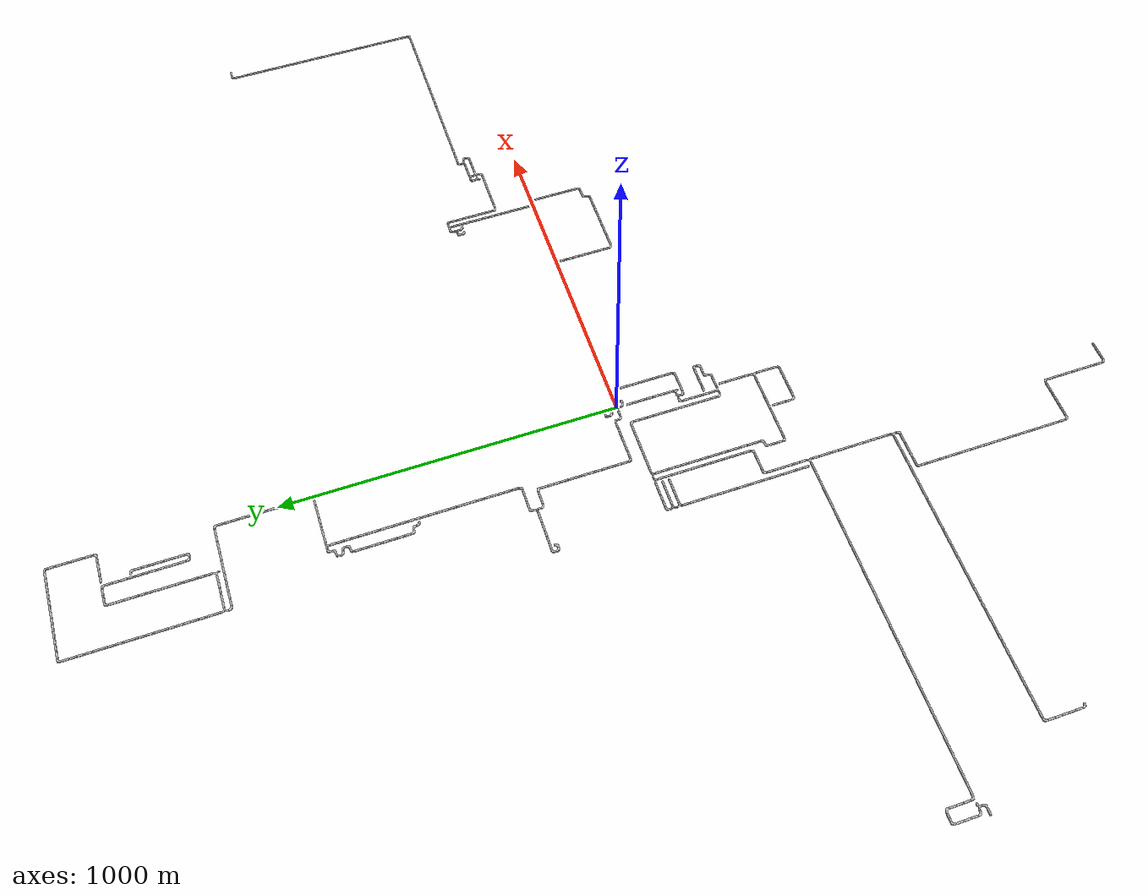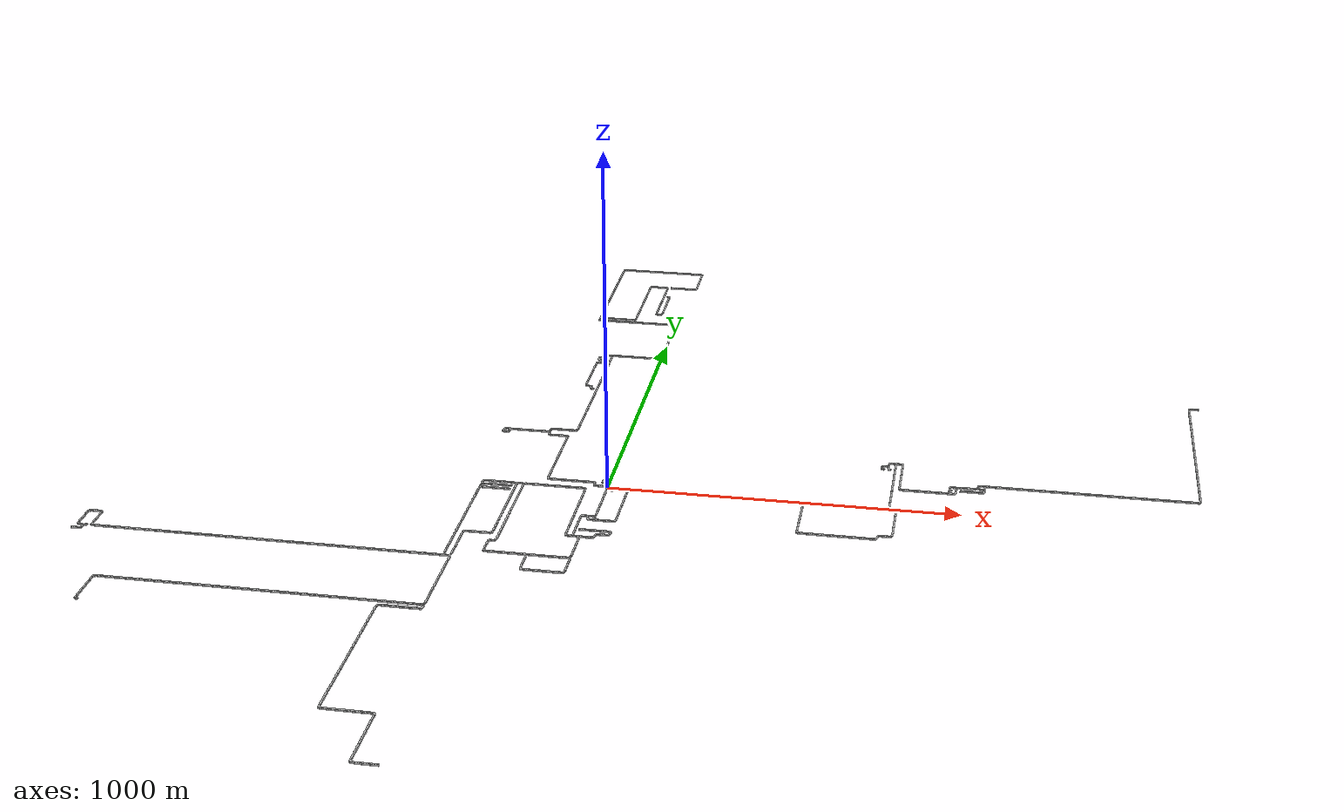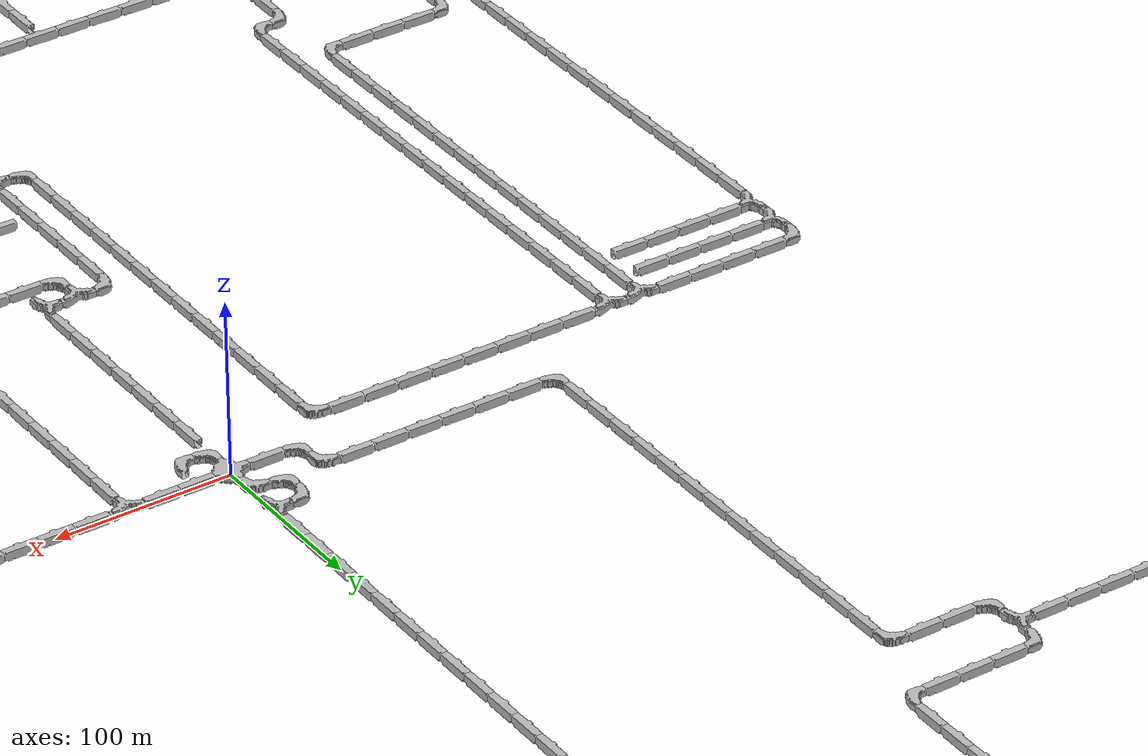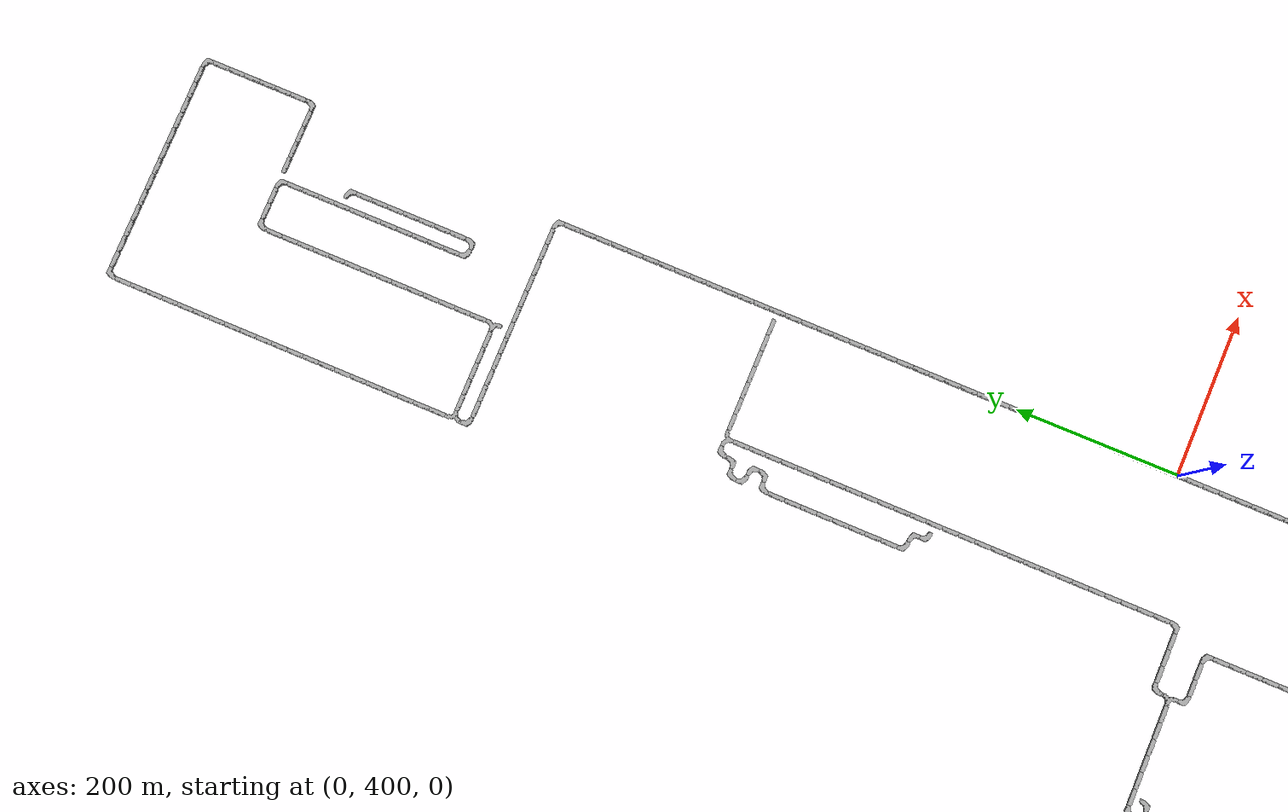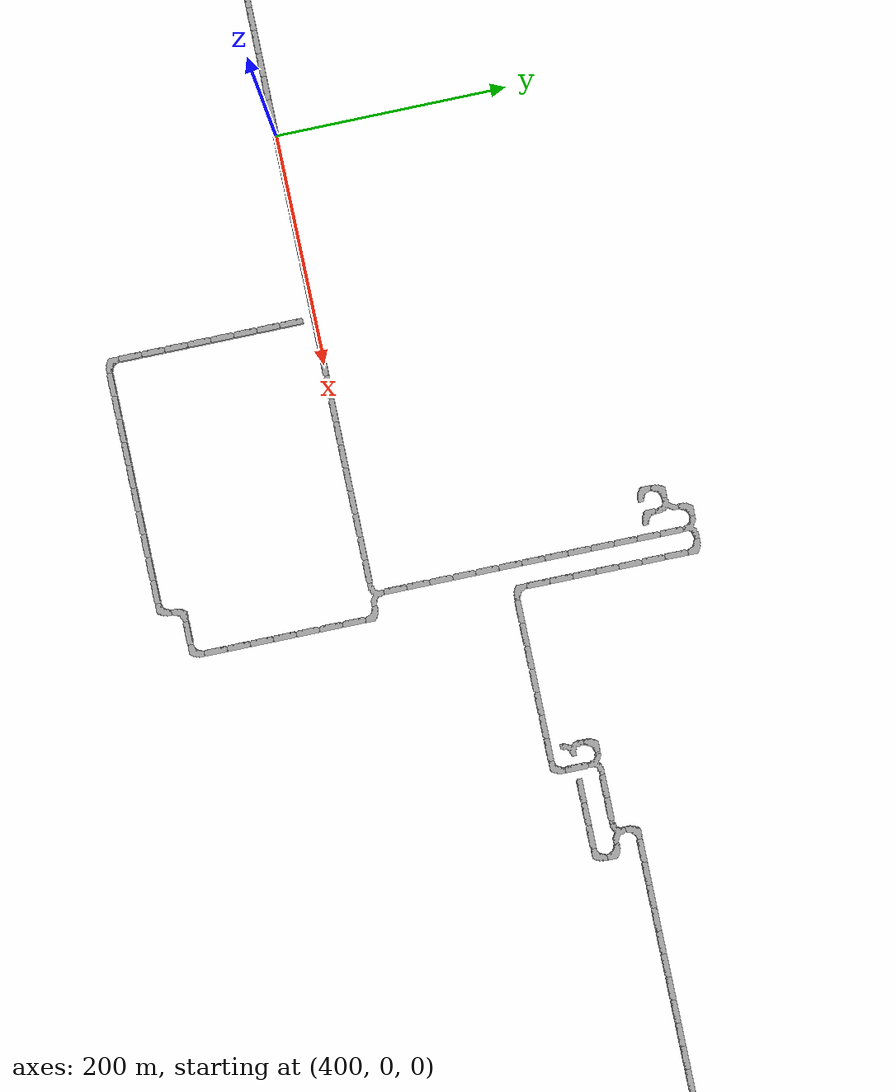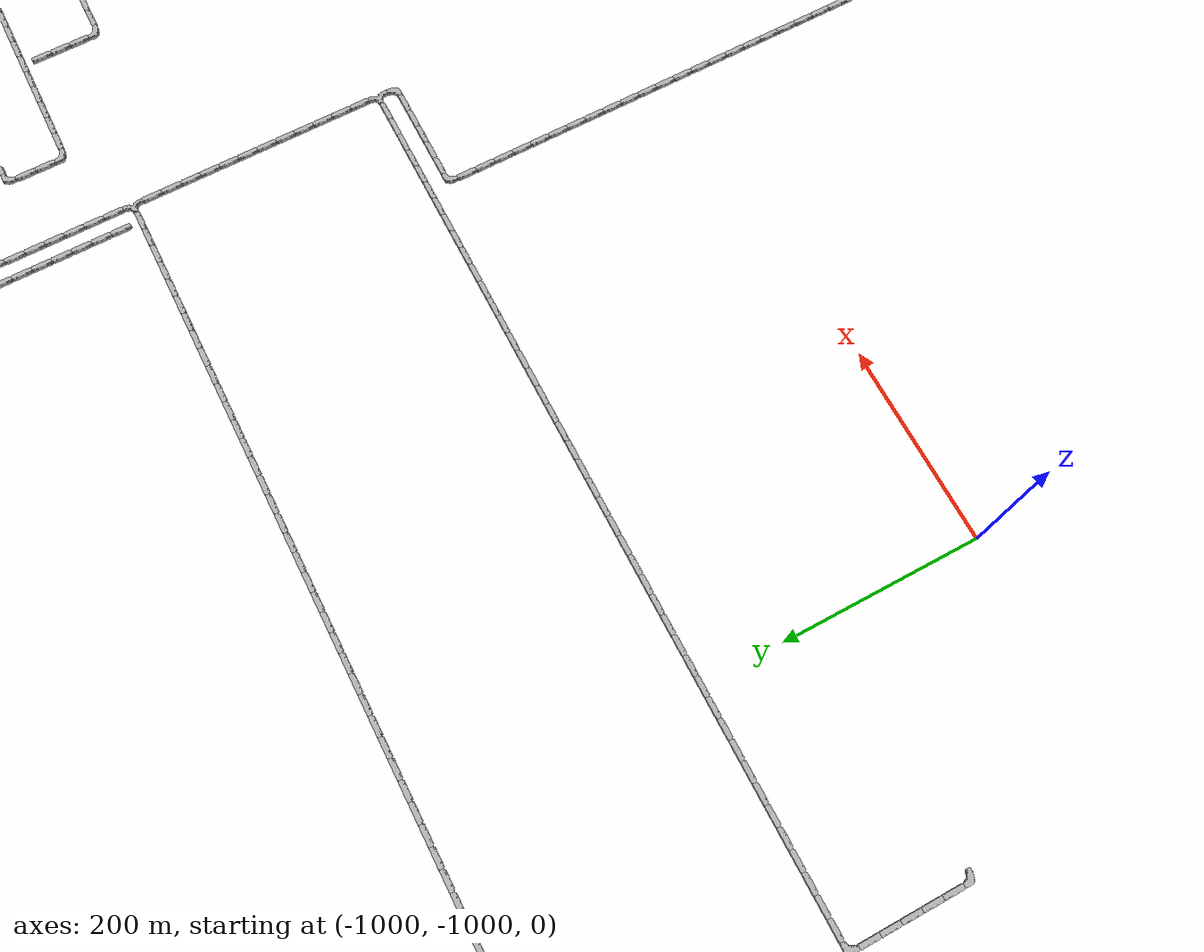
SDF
<sdf version="1.6">
 <world name="cave_16000_64">
  <include>
   <static>true</static>
   <name>cave_0_0</name>
   <pose>0 0 0 0 0 -1.5707963267948966</pose>
   <uri>model://cave_4way_20m</uri>
  </include>
  <include>
   <static>true</static>
   <name>cave_1_0</name>
   <pose>20 0 0 0 0 1.5707963267948966</pose>
   <uri>model://cave_straight_20m</uri>
  </include>
  <include>
   <static>true</static>
   <name>cave_2_0</name>
   <pose>40 0 0 0 0 1.5707963267948966</pose>
   <uri>model://cave_straight_20m</uri>
  </include>
  <include>
   <static>true</static>
   <name>cave_3_0</name>
   <pose>60 0 0 0 0 3.141592653589793</pose>
   <uri>model://cave_3way_20m</uri>
  </include>
  <include>
   <static>true</static>
   <name>cave_4_0</name>
   <pose>80 0 0 0 0 1.5707963267948966</pose>
   <uri>model://cave_straight_20m</uri>
  </include>
  <include>
   <static>true</static>
   <name>cave_5_0</name>
   <pose>100 0 0 0 0 1.5707963267948966</pose>
   <uri>model://cave_straight_20m</uri>
  </include>
  <include>
   <static>true</static>
   <name>cave_6_0</name>
   <pose>120 0 0 0 0 1.5707963267948966</pose>
   <uri>model://cave_straight_20m</uri>
  </include>
  <include>
   <static>true</static>
   <name>cave_7_0</name>
   <pose>140 0 0 0 0 1.5707963267948966</pose>
   <uri>model://cave_straight_20m</uri>
  </include>
  <include>
   <static>true</static>
   <name>cave_8_0</name>
   <pose>160 0 0 0 0 1.5707963267948966</pose>
   <uri>model://cave_straight_20m</uri>
  </include>
  <include>
   <static>true</static>
   <name>cave_9_0</name>
   <pose>180 0 0 0 0 1.5707963267948966</pose>
   <uri>model://cave_straight_20m</uri>
  </include>
  <include>
   <static>true</static>
   <name>cave_10_0</name>
   <pose>200 0 0 0 0 1.5707963267948966</pose>
   <uri>model://cave_straight_20m</uri>
  </include>
  <include>
   <static>true</static>
   <name>cave_11_0</name>
   <pose>220 0 0 0 0 1.5707963267948966</pose>
   <uri>model://cave_straight_20m</uri>
  </include>
  <include>
   <static>true</static>
   <name>cave_12_0</name>
   <pose>240 0 0 0 0 1.5707963267948966</pose>
   <uri>model://cave_straight_20m</uri>
  </include>
  <include>
   <static>true</static>
   <name>cave_13_0</name>
   <pose>260 0 0 0 0 1.5707963267948966</pose>
   <uri>model://cave_straight_20m</uri>
  </include>
  <include>
   <static>true</static>
   <name>cave_14_0</name>
   <pose>280 0 0 0 0 1.5707963267948966</pose>
   <uri>model://cave_straight_20m</uri>
  </include>
  <include>
   <static>true</static>
   <name>cave_15_0</name>
   <pose>300 0 0 0 0 1.5707963267948966</pose>
   <uri>model://cave_straight_20m</uri>
  </include>
  <include>
   <static>true</static>
   <name>cave_16_0</name>
   <pose>320 0 0 0 0 1.5707963267948966</pose>
   <uri>model://cave_straight_20m</uri>
  </include>
  <include>
   <static>true</static>
   <name>cave_17_0</name>
   <pose>340 0 0 0 0 1.5707963267948966</pose>
   <uri>model://cave_straight_20m</uri>
  </include>
  <include>
   <static>true</static>
   <name>cave_18_0</name>
   <pose>360 0 0 0 0 1.5707963267948966</pose>
   <uri>model://cave_straight_20m</uri>
  </include>
  <include>
   <static>true</static>
   <name>cave_19_0</name>
   <pose>380 0 0 0 0 1.5707963267948966</pose>
   <uri>model://cave_straight_20m</uri>
  </include>
  <include>
   <static>true</static>
   <name>cave_20_0</name>
   <pose>400 0 0 0 0 1.5707963267948966</pose>
   <uri>model://cave_straight_20m</uri>
  </include>
  <include>
   <static>true</static>
   <name>cave_21_0</name>
   <pose>420 0 0 0 0 1.5707963267948966</pose>
   <uri>model://cave_straight_20m</uri>
  </include>
  <include>
   <static>true</static>
   <name>cave_22_0</name>
   <pose>440 0 0 0 0 1.5707963267948966</pose>
   <uri>model://cave_straight_20m</uri>
  </include>
  <include>
   <static>true</static>
   <name>cave_23_0</name>
   <pose>460 0 0 0 0 1.5707963267948966</pose>
   <uri>model://cave_straight_20m</uri>
  </include>
  <include>
   <static>true</static>
   <name>cave_24_0</name>
   <pose>480 0 0 0 0 1.5707963267948966</pose>
   <uri>model://cave_straight_20m</uri>
  </include>
  <include>
   <static>true</static>
   <name>cave_25_0</name>
   <pose>500 0 0 0 0 1.5707963267948966</pose>
   <uri>model://cave_straight_20m</uri>
  </include>
  <include>
   <static>true</static>
   <name>cave_26_0</name>
   <pose>520 0 0 0 0 1.5707963267948966</pose>
   <uri>model://cave_straight_20m</uri>
  </include>
  <include>
   <static>true</static>
   <name>cave_27_0</name>
   <pose>540 0 0 0 0 1.5707963267948966</pose>
   <uri>model://cave_straight_20m</uri>
  </include>
  <include>
   <static>true</static>
   <name>cave_28_0</name>
   <pose>560 0 0 0 0 1.5707963267948966</pose>
   <uri>model://cave_straight_20m</uri>
  </include>
  <include>
   <static>true</static>
   <name>cave_29_0</name>
   <pose>580 0 0 0 0 1.5707963267948966</pose>
   <uri>model://cave_straight_20m</uri>
  </include>
  <include>
   <static>true</static>
   <name>cave_30_0</name>
   <pose>600 0 0 0 0 1.5707963267948966</pose>
   <uri>model://cave_straight_20m</uri>
  </include>
  <include>
   <static>true</static>
   <name>cave_31_0</name>
   <pose>620 0 0 0 0 1.5707963267948966</pose>
   <uri>model://cave_straight_20m</uri>
  </include>
  <include>
   <static>true</static>
   <name>cave_32_0</name>
   <pose>640 0 0 0 0 1.5707963267948966</pose>
   <uri>model://cave_straight_20m</uri>
  </include>
  <include>
   <static>true</static>
   <name>cave_33_0</name>
   <pose>660 0 0 0 0 1.5707963267948966</pose>
   <uri>model://cave_straight_20m</uri>
  </include>
  <include>
   <static>true</static>
   <name>cave_34_0</name>
   <pose>680 0 0 0 0 1.5707963267948966</pose>
   <uri>model://cave_straight_20m</uri>
  </include>
  <include>
   <static>true</static>
   <name>cave_35_0</name>
   <pose>700 0 0 0 0 1.5707963267948966</pose>
   <uri>model://cave_straight_20m</uri>
  </include>
  <include>
   <static>true</static>
   <name>cave_36_0</name>
   <pose>720 0 0 0 0 1.5707963267948966</pose>
   <uri>model://cave_straight_20m</uri>
  </include>
  <include>
   <static>true</static>
   <name>cave_37_0</name>
   <pose>740 0 0 0 0 1.5707963267948966</pose>
   <uri>model://cave_straight_20m</uri>
  </include>
  <include>
   <static>true</static>
   <name>cave_38_0</name>
   <pose>760 0 0 0 0 1.5707963267948966</pose>
   <uri>model://cave_straight_20m</uri>
  </include>
  <include>
   <static>true</static>
   <name>cave_39_0</name>
   <pose>780 0 0 0 0 1.5707963267948966</pose>
   <uri>model://cave_straight_20m</uri>
  </include>
  <include>
   <static>true</static>
   <name>cave_40_0</name>
   <pose>800 0 0 0 0 0.0</pose>
   <uri>model://cave_3way_20m</uri>
  </include>
  <include>
   <static>true</static>
   <name>cave_41_0</name>
   <pose>820 0 0 0 0 3.141592653589793</pose>
   <uri>model://cave_L_20m</uri>
  </include>
  <include>
   <static>true</static>
   <name>cave_41_-1</name>
   <pose>820 -20 0 0 0 0.0</pose>
   <uri>model://cave_straight_20m</uri>
  </include>
  <include>
   <static>true</static>
   <name>cave_41_-2</name>
   <pose>820 -40 0 0 0 0.0</pose>
   <uri>model://cave_straight_20m</uri>
  </include>
  <include>
   <static>true</static>
   <name>cave_41_-3</name>
   <pose>820 -60 0 0 0 0.0</pose>
   <uri>model://cave_straight_20m</uri>
  </include>
  <include>
   <static>true</static>
   <name>cave_41_-4</name>
   <pose>820 -80 0 0 0 0.0</pose>
   <uri>model://cave_straight_20m</uri>
  </include>
  <include>
   <static>true</static>
   <name>cave_41_-5</name>
   <pose>820 -100 0 0 0 0.0</pose>
   <uri>model://cave_straight_20m</uri>
  </include>
  <include>
   <static>true</static>
   <name>cave_41_-6</name>
   <pose>820 -120 0 0 0 0.0</pose>
   <uri>model://cave_straight_20m</uri>
  </include>
  <include>
   <static>true</static>
   <name>cave_41_-7</name>
   <pose>820 -140 0 0 0 0.0</pose>
   <uri>model://cave_straight_20m</uri>
  </include>
  <include>
   <static>true</static>
   <name>cave_41_-8</name>
   <pose>820 -160 0 0 0 1.5707963267948966</pose>
   <uri>model://cave_L_20m</uri>
  </include>
  <include>
   <static>true</static>
   <name>cave_40_-8</name>
   <pose>800 -160 0 0 0 1.5707963267948966</pose>
   <uri>model://cave_straight_20m</uri>
  </include>
  <include>
   <static>true</static>
   <name>cave_39_-8</name>
   <pose>780 -160 0 0 0 -1.5707963267948966</pose>
   <uri>model://cave_L_20m</uri>
  </include>
  <include>
   <static>true</static>
   <name>cave_39_-9</name>
   <pose>780 -180 0 0 0 1.5707963267948966</pose>
   <uri>model://cave_L_20m</uri>
  </include>
  <include>
   <static>true</static>
   <name>cave_38_-9</name>
   <pose>760 -180 0 0 0 1.5707963267948966</pose>
   <uri>model://cave_straight_20m</uri>
  </include>
  <include>
   <static>true</static>
   <name>cave_37_-9</name>
   <pose>740 -180 0 0 0 1.5707963267948966</pose>
   <uri>model://cave_straight_20m</uri>
  </include>
  <include>
   <static>true</static>
   <name>cave_36_-9</name>
   <pose>720 -180 0 0 0 1.5707963267948966</pose>
   <uri>model://cave_straight_20m</uri>
  </include>
  <include>
   <static>true</static>
   <name>cave_35_-9</name>
   <pose>700 -180 0 0 0 1.5707963267948966</pose>
   <uri>model://cave_straight_20m</uri>
  </include>
  <include>
   <static>true</static>
   <name>cave_34_-9</name>
   <pose>680 -180 0 0 0 1.5707963267948966</pose>
   <uri>model://cave_straight_20m</uri>
  </include>
  <include>
   <static>true</static>
   <name>cave_33_-9</name>
   <pose>660 -180 0 0 0 1.5707963267948966</pose>
   <uri>model://cave_straight_20m</uri>
  </include>
  <include>
   <static>true</static>
   <name>cave_32_-9</name>
   <pose>640 -180 0 0 0 1.5707963267948966</pose>
   <uri>model://cave_straight_20m</uri>
  </include>
  <include>
   <static>true</static>
   <name>cave_31_-9</name>
   <pose>620 -180 0 0 0 1.5707963267948966</pose>
   <uri>model://cave_straight_20m</uri>
  </include>
  <include>
   <static>true</static>
   <name>cave_30_-9</name>
   <pose>600 -180 0 0 0 1.5707963267948966</pose>
   <uri>model://cave_straight_20m</uri>
  </include>
  <include>
   <static>true</static>
   <name>cave_29_-9</name>
   <pose>580 -180 0 0 0 1.5707963267948966</pose>
   <uri>model://cave_straight_20m</uri>
  </include>
  <include>
   <static>true</static>
   <name>cave_28_-9</name>
   <pose>560 -180 0 0 0 0.0</pose>
   <uri>model://cave_L_20m</uri>
  </include>
  <include>
   <static>true</static>
   <name>cave_28_-8</name>
   <pose>560 -160 0 0 0 0.0</pose>
   <uri>model://cave_straight_20m</uri>
  </include>
  <include>
   <static>true</static>
   <name>cave_28_-7</name>
   <pose>560 -140 0 0 0 0.0</pose>
   <uri>model://cave_straight_20m</uri>
  </include>
  <include>
   <static>true</static>
   <name>cave_28_-6</name>
   <pose>560 -120 0 0 0 0.0</pose>
   <uri>model://cave_straight_20m</uri>
  </include>
  <include>
   <static>true</static>
   <name>cave_28_-5</name>
   <pose>560 -100 0 0 0 0.0</pose>
   <uri>model://cave_straight_20m</uri>
  </include>
  <include>
   <static>true</static>
   <name>cave_28_-4</name>
   <pose>560 -80 0 0 0 0.0</pose>
   <uri>model://cave_straight_20m</uri>
  </include>
  <include>
   <static>true</static>
   <name>cave_28_-3</name>
   <pose>560 -60 0 0 0 0.0</pose>
   <uri>model://cave_straight_20m</uri>
  </include>
  <include>
   <static>true</static>
   <name>cave_28_-2</name>
   <pose>560 -40 0 0 0 0.0</pose>
   <uri>model://cave_straight_20m</uri>
  </include>
  <include>
   <static>true</static>
   <name>cave_28_-1</name>
   <pose>560 -20 0 0 0 0.0</pose>
   <uri>model://cave_straight_20m</uri>
  </include>
  <include>
   <static>true</static>
   <name>cave_40_1</name>
   <pose>800 20 0 0 0 0.0</pose>
   <uri>model://cave_straight_20m</uri>
  </include>
  <include>
   <static>true</static>
   <name>cave_40_2</name>
   <pose>800 40 0 0 0 0.0</pose>
   <uri>model://cave_straight_20m</uri>
  </include>
  <include>
   <static>true</static>
   <name>cave_40_3</name>
   <pose>800 60 0 0 0 0.0</pose>
   <uri>model://cave_straight_20m</uri>
  </include>
  <include>
   <static>true</static>
   <name>cave_40_4</name>
   <pose>800 80 0 0 0 0.0</pose>
   <uri>model://cave_straight_20m</uri>
  </include>
  <include>
   <static>true</static>
   <name>cave_40_5</name>
   <pose>800 100 0 0 0 0.0</pose>
   <uri>model://cave_straight_20m</uri>
  </include>
  <include>
   <static>true</static>
   <name>cave_40_6</name>
   <pose>800 120 0 0 0 0.0</pose>
   <uri>model://cave_straight_20m</uri>
  </include>
  <include>
   <static>true</static>
   <name>cave_40_7</name>
   <pose>800 140 0 0 0 0.0</pose>
   <uri>model://cave_straight_20m</uri>
  </include>
  <include>
   <static>true</static>
   <name>cave_40_8</name>
   <pose>800 160 0 0 0 0.0</pose>
   <uri>model://cave_straight_20m</uri>
  </include>
  <include>
   <static>true</static>
   <name>cave_40_9</name>
   <pose>800 180 0 0 0 0.0</pose>
   <uri>model://cave_straight_20m</uri>
  </include>
  <include>
   <static>true</static>
   <name>cave_40_10</name>
   <pose>800 200 0 0 0 0.0</pose>
   <uri>model://cave_straight_20m</uri>
  </include>
  <include>
   <static>true</static>
   <name>cave_40_11</name>
   <pose>800 220 0 0 0 0.0</pose>
   <uri>model://cave_straight_20m</uri>
  </include>
  <include>
   <static>true</static>
   <name>cave_40_12</name>
   <pose>800 240 0 0 0 0.0</pose>
   <uri>model://cave_straight_20m</uri>
  </include>
  <include>
   <static>true</static>
   <name>cave_40_13</name>
   <pose>800 260 0 0 0 0.0</pose>
   <uri>model://cave_straight_20m</uri>
  </include>
  <include>
   <static>true</static>
   <name>cave_40_14</name>
   <pose>800 280 0 0 0 3.141592653589793</pose>
   <uri>model://cave_3way_20m</uri>
  </include>
  <include>
   <static>true</static>
   <name>cave_41_14</name>
   <pose>820 280 0 0 0 3.141592653589793</pose>
   <uri>model://cave_L_20m</uri>
  </include>
  <include>
   <static>true</static>
   <name>cave_41_13</name>
   <pose>820 260 0 0 0 0.0</pose>
   <uri>model://cave_straight_20m</uri>
  </include>
  <include>
   <static>true</static>
   <name>cave_41_12</name>
   <pose>820 240 0 0 0 0.0</pose>
   <uri>model://cave_straight_20m</uri>
  </include>
  <include>
   <static>true</static>
   <name>cave_41_11</name>
   <pose>820 220 0 0 0 0.0</pose>
   <uri>model://cave_straight_20m</uri>
  </include>
  <include>
   <static>true</static>
   <name>cave_41_10</name>
   <pose>820 200 0 0 0 0.0</pose>
   <uri>model://cave_straight_20m</uri>
  </include>
  <include>
   <static>true</static>
   <name>cave_41_9</name>
   <pose>820 180 0 0 0 0.0</pose>
   <uri>model://cave_straight_20m</uri>
  </include>
  <include>
   <static>true</static>
   <name>cave_41_8</name>
   <pose>820 160 0 0 0 0.0</pose>
   <uri>model://cave_straight_20m</uri>
  </include>
  <include>
   <static>true</static>
   <name>cave_41_7</name>
   <pose>820 140 0 0 0 0.0</pose>
   <uri>model://cave_straight_20m</uri>
  </include>
  <include>
   <static>true</static>
   <name>cave_41_6</name>
   <pose>820 120 0 0 0 0.0</pose>
   <uri>model://cave_L_20m</uri>
  </include>
  <include>
   <static>true</static>
   <name>cave_42_6</name>
   <pose>840 120 0 0 0 1.5707963267948966</pose>
   <uri>model://cave_straight_20m</uri>
  </include>
  <include>
   <static>true</static>
   <name>cave_43_6</name>
   <pose>860 120 0 0 0 1.5707963267948966</pose>
   <uri>model://cave_straight_20m</uri>
  </include>
  <include>
   <static>true</static>
   <name>cave_44_6</name>
   <pose>880 120 0 0 0 1.5707963267948966</pose>
   <uri>model://cave_straight_20m</uri>
  </include>
  <include>
   <static>true</static>
   <name>cave_45_6</name>
   <pose>900 120 0 0 0 1.5707963267948966</pose>
   <uri>model://cave_straight_20m</uri>
  </include>
  <include>
   <static>true</static>
   <name>cave_46_6</name>
   <pose>920 120 0 0 0 1.5707963267948966</pose>
   <uri>model://cave_straight_20m</uri>
  </include>
  <include>
   <static>true</static>
   <name>cave_47_6</name>
   <pose>940 120 0 0 0 1.5707963267948966</pose>
   <uri>model://cave_straight_20m</uri>
  </include>
  <include>
   <static>true</static>
   <name>cave_48_6</name>
   <pose>960 120 0 0 0 1.5707963267948966</pose>
   <uri>model://cave_straight_20m</uri>
  </include>
  <include>
   <static>true</static>
   <name>cave_49_6</name>
   <pose>980 120 0 0 0 1.5707963267948966</pose>
   <uri>model://cave_L_20m</uri>
  </include>
  <include>
   <static>true</static>
   <name>cave_49_7</name>
   <pose>980 140 0 0 0 0.0</pose>
   <uri>model://cave_straight_20m</uri>
  </include>
  <include>
   <static>true</static>
   <name>cave_49_8</name>
   <pose>980 160 0 0 0 3.141592653589793</pose>
   <uri>model://cave_3way_20m</uri>
  </include>
  <include>
   <static>true</static>
   <name>cave_50_8</name>
   <pose>1000 160 0 0 0 1.5707963267948966</pose>
   <uri>model://cave_straight_20m</uri>
  </include>
  <include>
   <static>true</static>
   <name>cave_51_8</name>
   <pose>1020 160 0 0 0 1.5707963267948966</pose>
   <uri>model://cave_straight_20m</uri>
  </include>
  <include>
   <static>true</static>
   <name>cave_52_8</name>
   <pose>1040 160 0 0 0 0.0</pose>
   <uri>model://cave_3way_20m</uri>
  </include>
  <include>
   <static>true</static>
   <name>cave_53_8</name>
   <pose>1060 160 0 0 0 3.141592653589793</pose>
   <uri>model://cave_L_20m</uri>
  </include>
  <include>
   <static>true</static>
   <name>cave_53_7</name>
   <pose>1060 140 0 0 0 1.5707963267948966</pose>
   <uri>model://cave_L_20m</uri>
  </include>
  <include>
   <static>true</static>
   <name>cave_52_7</name>
   <pose>1040 140 0 0 0 1.5707963267948966</pose>
   <uri>model://cave_straight_20m</uri>
  </include>
  <include>
   <static>true</static>
   <name>cave_51_7</name>
   <pose>1020 140 0 0 0 1.5707963267948966</pose>
   <uri>model://cave_straight_20m</uri>
  </include>
  <include>
   <static>true</static>
   <name>cave_50_7</name>
   <pose>1000 140 0 0 0 1.5707963267948966</pose>
   <uri>model://cave_straight_20m</uri>
  </include>
  <include>
   <static>true</static>
   <name>cave_52_9</name>
   <pose>1040 180 0 0 0 -1.5707963267948966</pose>
   <uri>model://cave_L_20m</uri>
  </include>
  <include>
   <static>true</static>
   <name>cave_53_9</name>
   <pose>1060 180 0 0 0 1.5707963267948966</pose>
   <uri>model://cave_straight_20m</uri>
  </include>
  <include>
   <static>true</static>
   <name>cave_54_9</name>
   <pose>1080 180 0 0 0 1.5707963267948966</pose>
   <uri>model://cave_straight_20m</uri>
  </include>
  <include>
   <static>true</static>
   <name>cave_55_9</name>
   <pose>1100 180 0 0 0 1.5707963267948966</pose>
   <uri>model://cave_straight_20m</uri>
  </include>
  <include>
   <static>true</static>
   <name>cave_56_9</name>
   <pose>1120 180 0 0 0 1.5707963267948966</pose>
   <uri>model://cave_straight_20m</uri>
  </include>
  <include>
   <static>true</static>
   <name>cave_57_9</name>
   <pose>1140 180 0 0 0 1.5707963267948966</pose>
   <uri>model://cave_straight_20m</uri>
  </include>
  <include>
   <static>true</static>
   <name>cave_58_9</name>
   <pose>1160 180 0 0 0 1.5707963267948966</pose>
   <uri>model://cave_straight_20m</uri>
  </include>
  <include>
   <static>true</static>
   <name>cave_59_9</name>
   <pose>1180 180 0 0 0 1.5707963267948966</pose>
   <uri>model://cave_straight_20m</uri>
  </include>
  <include>
   <static>true</static>
   <name>cave_60_9</name>
   <pose>1200 180 0 0 0 1.5707963267948966</pose>
   <uri>model://cave_straight_20m</uri>
  </include>
  <include>
   <static>true</static>
   <name>cave_61_9</name>
   <pose>1220 180 0 0 0 1.5707963267948966</pose>
   <uri>model://cave_straight_20m</uri>
  </include>
  <include>
   <static>true</static>
   <name>cave_62_9</name>
   <pose>1240 180 0 0 0 1.5707963267948966</pose>
   <uri>model://cave_straight_20m</uri>
  </include>
  <include>
   <static>true</static>
   <name>cave_63_9</name>
   <pose>1260 180 0 0 0 1.5707963267948966</pose>
   <uri>model://cave_straight_20m</uri>
  </include>
  <include>
   <static>true</static>
   <name>cave_64_9</name>
   <pose>1280 180 0 0 0 1.5707963267948966</pose>
   <uri>model://cave_straight_20m</uri>
  </include>
  <include>
   <static>true</static>
   <name>cave_65_9</name>
   <pose>1300 180 0 0 0 1.5707963267948966</pose>
   <uri>model://cave_straight_20m</uri>
  </include>
  <include>
   <static>true</static>
   <name>cave_66_9</name>
   <pose>1320 180 0 0 0 1.5707963267948966</pose>
   <uri>model://cave_straight_20m</uri>
  </include>
  <include>
   <static>true</static>
   <name>cave_67_9</name>
   <pose>1340 180 0 0 0 1.5707963267948966</pose>
   <uri>model://cave_straight_20m</uri>
  </include>
  <include>
   <static>true</static>
   <name>cave_68_9</name>
   <pose>1360 180 0 0 0 1.5707963267948966</pose>
   <uri>model://cave_straight_20m</uri>
  </include>
  <include>
   <static>true</static>
   <name>cave_69_9</name>
   <pose>1380 180 0 0 0 1.5707963267948966</pose>
   <uri>model://cave_straight_20m</uri>
  </include>
  <include>
   <static>true</static>
   <name>cave_70_9</name>
   <pose>1400 180 0 0 0 1.5707963267948966</pose>
   <uri>model://cave_straight_20m</uri>
  </include>
  <include>
   <static>true</static>
   <name>cave_71_9</name>
   <pose>1420 180 0 0 0 1.5707963267948966</pose>
   <uri>model://cave_straight_20m</uri>
  </include>
  <include>
   <static>true</static>
   <name>cave_72_9</name>
   <pose>1440 180 0 0 0 1.5707963267948966</pose>
   <uri>model://cave_straight_20m</uri>
  </include>
  <include>
   <static>true</static>
   <name>cave_73_9</name>
   <pose>1460 180 0 0 0 1.5707963267948966</pose>
   <uri>model://cave_straight_20m</uri>
  </include>
  <include>
   <static>true</static>
   <name>cave_74_9</name>
   <pose>1480 180 0 0 0 1.5707963267948966</pose>
   <uri>model://cave_straight_20m</uri>
  </include>
  <include>
   <static>true</static>
   <name>cave_75_9</name>
   <pose>1500 180 0 0 0 1.5707963267948966</pose>
   <uri>model://cave_straight_20m</uri>
  </include>
  <include>
   <static>true</static>
   <name>cave_76_9</name>
   <pose>1520 180 0 0 0 1.5707963267948966</pose>
   <uri>model://cave_straight_20m</uri>
  </include>
  <include>
   <static>true</static>
   <name>cave_77_9</name>
   <pose>1540 180 0 0 0 1.5707963267948966</pose>
   <uri>model://cave_straight_20m</uri>
  </include>
  <include>
   <static>true</static>
   <name>cave_78_9</name>
   <pose>1560 180 0 0 0 1.5707963267948966</pose>
   <uri>model://cave_straight_20m</uri>
  </include>
  <include>
   <static>true</static>
   <name>cave_79_9</name>
   <pose>1580 180 0 0 0 1.5707963267948966</pose>
   <uri>model://cave_straight_20m</uri>
  </include>
  <include>
   <static>true</static>
   <name>cave_80_9</name>
   <pose>1600 180 0 0 0 1.5707963267948966</pose>
   <uri>model://cave_straight_20m</uri>
  </include>
  <include>
   <static>true</static>
   <name>cave_81_9</name>
   <pose>1620 180 0 0 0 1.5707963267948966</pose>
   <uri>model://cave_straight_20m</uri>
  </include>
  <include>
   <static>true</static>
   <name>cave_82_9</name>
   <pose>1640 180 0 0 0 1.5707963267948966</pose>
   <uri>model://cave_straight_20m</uri>
  </include>
  <include>
   <static>true</static>
   <name>cave_83_9</name>
   <pose>1660 180 0 0 0 1.5707963267948966</pose>
   <uri>model://cave_L_20m</uri>
  </include>
  <include>
   <static>true</static>
   <name>cave_83_10</name>
   <pose>1660 200 0 0 0 0.0</pose>
   <uri>model://cave_straight_20m</uri>
  </include>
  <include>
   <static>true</static>
   <name>cave_83_11</name>
   <pose>1660 220 0 0 0 0.0</pose>
   <uri>model://cave_straight_20m</uri>
  </include>
  <include>
   <static>true</static>
   <name>cave_83_12</name>
   <pose>1660 240 0 0 0 0.0</pose>
   <uri>model://cave_straight_20m</uri>
  </include>
  <include>
   <static>true</static>
   <name>cave_83_13</name>
   <pose>1660 260 0 0 0 0.0</pose>
   <uri>model://cave_straight_20m</uri>
  </include>
  <include>
   <static>true</static>
   <name>cave_83_14</name>
   <pose>1660 280 0 0 0 0.0</pose>
   <uri>model://cave_straight_20m</uri>
  </include>
  <include>
   <static>true</static>
   <name>cave_83_15</name>
   <pose>1660 300 0 0 0 0.0</pose>
   <uri>model://cave_straight_20m</uri>
  </include>
  <include>
   <static>true</static>
   <name>cave_83_16</name>
   <pose>1660 320 0 0 0 0.0</pose>
   <uri>model://cave_straight_20m</uri>
  </include>
  <include>
   <static>true</static>
   <name>cave_83_17</name>
   <pose>1660 340 0 0 0 0.0</pose>
   <uri>model://cave_straight_20m</uri>
  </include>
  <include>
   <static>true</static>
   <name>cave_83_18</name>
   <pose>1660 360 0 0 0 0.0</pose>
   <uri>model://cave_straight_20m</uri>
  </include>
  <include>
   <static>true</static>
   <name>cave_83_19</name>
   <pose>1660 380 0 0 0 0.0</pose>
   <uri>model://cave_straight_20m</uri>
  </include>
  <include>
   <static>true</static>
   <name>cave_83_20</name>
   <pose>1660 400 0 0 0 0.0</pose>
   <uri>model://cave_straight_20m</uri>
  </include>
  <include>
   <static>true</static>
   <name>cave_83_21</name>
   <pose>1660 420 0 0 0 0.0</pose>
   <uri>model://cave_straight_20m</uri>
  </include>
  <include>
   <static>true</static>
   <name>cave_83_22</name>
   <pose>1660 440 0 0 0 0.0</pose>
   <uri>model://cave_straight_20m</uri>
  </include>
  <include>
   <static>true</static>
   <name>cave_83_23</name>
   <pose>1660 460 0 0 0 0.0</pose>
   <uri>model://cave_straight_20m</uri>
  </include>
  <include>
   <static>true</static>
   <name>cave_83_24</name>
   <pose>1660 480 0 0 0 0.0</pose>
   <uri>model://cave_straight_20m</uri>
  </include>
  <include>
   <static>true</static>
   <name>cave_83_25</name>
   <pose>1660 500 0 0 0 0.0</pose>
   <uri>model://cave_straight_20m</uri>
  </include>
  <include>
   <static>true</static>
   <name>cave_83_26</name>
   <pose>1660 520 0 0 0 0.0</pose>
   <uri>model://cave_straight_20m</uri>
  </include>
  <include>
   <static>true</static>
   <name>cave_83_27</name>
   <pose>1660 540 0 0 0 0.0</pose>
   <uri>model://cave_straight_20m</uri>
  </include>
  <include>
   <static>true</static>
   <name>cave_83_28</name>
   <pose>1660 560 0 0 0 0.0</pose>
   <uri>model://cave_straight_20m</uri>
  </include>
  <include>
   <static>true</static>
   <name>cave_83_29</name>
   <pose>1660 580 0 0 0 0.0</pose>
   <uri>model://cave_straight_20m</uri>
  </include>
  <include>
   <static>true</static>
   <name>cave_83_30</name>
   <pose>1660 600 0 0 0 0.0</pose>
   <uri>model://cave_straight_20m</uri>
  </include>
  <include>
   <static>true</static>
   <name>cave_83_31</name>
   <pose>1660 620 0 0 0 0.0</pose>
   <uri>model://cave_straight_20m</uri>
  </include>
  <include>
   <static>true</static>
   <name>cave_83_32</name>
   <pose>1660 640 0 0 0 0.0</pose>
   <uri>model://cave_straight_20m</uri>
  </include>
  <include>
   <static>true</static>
   <name>cave_83_33</name>
   <pose>1660 660 0 0 0 0.0</pose>
   <uri>model://cave_straight_20m</uri>
  </include>
  <include>
   <static>true</static>
   <name>cave_83_34</name>
   <pose>1660 680 0 0 0 0.0</pose>
   <uri>model://cave_straight_20m</uri>
  </include>
  <include>
   <static>true</static>
   <name>cave_83_35</name>
   <pose>1660 700 0 0 0 0.0</pose>
   <uri>model://cave_straight_20m</uri>
  </include>
  <include>
   <static>true</static>
   <name>cave_83_36</name>
   <pose>1660 720 0 0 0 0.0</pose>
   <uri>model://cave_straight_20m</uri>
  </include>
  <include>
   <static>true</static>
   <name>cave_83_37</name>
   <pose>1660 740 0 0 0 0.0</pose>
   <uri>model://cave_straight_20m</uri>
  </include>
  <include>
   <static>true</static>
   <name>cave_83_38</name>
   <pose>1660 760 0 0 0 0.0</pose>
   <uri>model://cave_straight_20m</uri>
  </include>
  <include>
   <static>true</static>
   <name>cave_83_39</name>
   <pose>1660 780 0 0 0 0.0</pose>
   <uri>model://cave_straight_20m</uri>
  </include>
  <include>
   <static>true</static>
   <name>cave_83_40</name>
   <pose>1660 800 0 0 0 -1.5707963267948966</pose>
   <uri>model://cave_L_20m</uri>
  </include>
  <include>
   <static>true</static>
   <name>cave_84_40</name>
   <pose>1680 800 0 0 0 1.5707963267948966</pose>
   <uri>model://cave_straight_20m</uri>
  </include>
  <include>
   <static>true</static>
   <name>cave_48_8</name>
   <pose>960 160 0 0 0 -1.5707963267948966</pose>
   <uri>model://cave_L_20m</uri>
  </include>
  <include>
   <static>true</static>
   <name>cave_48_7</name>
   <pose>960 140 0 0 0 -1.5707963267948966</pose>
   <uri>model://cave_3way_20m</uri>
  </include>
  <include>
   <static>true</static>
   <name>cave_39_14</name>
   <pose>780 280 0 0 0 -1.5707963267948966</pose>
   <uri>model://cave_L_20m</uri>
  </include>
  <include>
   <static>true</static>
   <name>cave_39_13</name>
   <pose>780 260 0 0 0 1.5707963267948966</pose>
   <uri>model://cave_3way_20m</uri>
  </include>
  <include>
   <static>true</static>
   <name>cave_39_12</name>
   <pose>780 240 0 0 0 0.0</pose>
   <uri>model://cave_L_20m</uri>
  </include>
  <include>
   <static>true</static>
   <name>cave_38_13</name>
   <pose>760 260 0 0 0 -1.5707963267948966</pose>
   <uri>model://cave_L_20m</uri>
  </include>
  <include>
   <static>true</static>
   <name>cave_38_12</name>
   <pose>760 240 0 0 0 0.0</pose>
   <uri>model://cave_L_20m</uri>
  </include>
  <include>
   <static>true</static>
   <name>cave_3_-1</name>
   <pose>60 -20 0 0 0 0.0</pose>
   <uri>model://cave_straight_20m</uri>
  </include>
  <include>
   <static>true</static>
   <name>cave_3_-2</name>
   <pose>60 -40 0 0 0 0.0</pose>
   <uri>model://cave_straight_20m</uri>
  </include>
  <include>
   <static>true</static>
   <name>cave_3_-3</name>
   <pose>60 -60 0 0 0 0.0</pose>
   <uri>model://cave_straight_20m</uri>
  </include>
  <include>
   <static>true</static>
   <name>cave_3_-4</name>
   <pose>60 -80 0 0 0 0.0</pose>
   <uri>model://cave_straight_20m</uri>
  </include>
  <include>
   <static>true</static>
   <name>cave_3_-5</name>
   <pose>60 -100 0 0 0 0.0</pose>
   <uri>model://cave_straight_20m</uri>
  </include>
  <include>
   <static>true</static>
   <name>cave_3_-6</name>
   <pose>60 -120 0 0 0 0.0</pose>
   <uri>model://cave_straight_20m</uri>
  </include>
  <include>
   <static>true</static>
   <name>cave_3_-7</name>
   <pose>60 -140 0 0 0 0.0</pose>
   <uri>model://cave_straight_20m</uri>
  </include>
  <include>
   <static>true</static>
   <name>cave_3_-8</name>
   <pose>60 -160 0 0 0 0.0</pose>
   <uri>model://cave_straight_20m</uri>
  </include>
  <include>
   <static>true</static>
   <name>cave_3_-9</name>
   <pose>60 -180 0 0 0 0.0</pose>
   <uri>model://cave_straight_20m</uri>
  </include>
  <include>
   <static>true</static>
   <name>cave_3_-10</name>
   <pose>60 -200 0 0 0 1.5707963267948966</pose>
   <uri>model://cave_L_20m</uri>
  </include>
  <include>
   <static>true</static>
   <name>cave_2_-10</name>
   <pose>40 -200 0 0 0 1.5707963267948966</pose>
   <uri>model://cave_straight_20m</uri>
  </include>
  <include>
   <static>true</static>
   <name>cave_1_-10</name>
   <pose>20 -200 0 0 0 1.5707963267948966</pose>
   <uri>model://cave_straight_20m</uri>
  </include>
  <include>
   <static>true</static>
   <name>cave_0_-10</name>
   <pose>0 -200 0 0 0 1.5707963267948966</pose>
   <uri>model://cave_straight_20m</uri>
  </include>
  <include>
   <static>true</static>
   <name>cave_-1_-10</name>
   <pose>-20 -200 0 0 0 0.0</pose>
   <uri>model://cave_L_20m</uri>
  </include>
  <include>
   <static>true</static>
   <name>cave_-1_-9</name>
   <pose>-20 -180 0 0 0 3.141592653589793</pose>
   <uri>model://cave_3way_20m</uri>
  </include>
  <include>
   <static>true</static>
   <name>cave_0_-9</name>
   <pose>0 -180 0 0 0 1.5707963267948966</pose>
   <uri>model://cave_3way_20m</uri>
  </include>
  <include>
   <static>true</static>
   <name>cave_0_-8</name>
   <pose>0 -160 0 0 0 0.0</pose>
   <uri>model://cave_straight_20m</uri>
  </include>
  <include>
   <static>true</static>
   <name>cave_0_-7</name>
   <pose>0 -140 0 0 0 0.0</pose>
   <uri>model://cave_straight_20m</uri>
  </include>
  <include>
   <static>true</static>
   <name>cave_0_-6</name>
   <pose>0 -120 0 0 0 0.0</pose>
   <uri>model://cave_straight_20m</uri>
  </include>
  <include>
   <static>true</static>
   <name>cave_0_-5</name>
   <pose>0 -100 0 0 0 0.0</pose>
   <uri>model://cave_straight_20m</uri>
  </include>
  <include>
   <static>true</static>
   <name>cave_0_-4</name>
   <pose>0 -80 0 0 0 0.0</pose>
   <uri>model://cave_straight_20m</uri>
  </include>
  <include>
   <static>true</static>
   <name>cave_0_-3</name>
   <pose>0 -60 0 0 0 0.0</pose>
   <uri>model://cave_straight_20m</uri>
  </include>
  <include>
   <static>true</static>
   <name>cave_0_-2</name>
   <pose>0 -40 0 0 0 0.0</pose>
   <uri>model://cave_straight_20m</uri>
  </include>
  <include>
   <static>true</static>
   <name>cave_-2_-9</name>
   <pose>-40 -180 0 0 0 -1.5707963267948966</pose>
   <uri>model://cave_L_20m</uri>
  </include>
  <include>
   <static>true</static>
   <name>cave_-2_-10</name>
   <pose>-40 -200 0 0 0 0.0</pose>
   <uri>model://cave_straight_20m</uri>
  </include>
  <include>
   <static>true</static>
   <name>cave_-2_-11</name>
   <pose>-40 -220 0 0 0 0.0</pose>
   <uri>model://cave_straight_20m</uri>
  </include>
  <include>
   <static>true</static>
   <name>cave_-2_-12</name>
   <pose>-40 -240 0 0 0 0.0</pose>
   <uri>model://cave_straight_20m</uri>
  </include>
  <include>
   <static>true</static>
   <name>cave_-2_-13</name>
   <pose>-40 -260 0 0 0 0.0</pose>
   <uri>model://cave_straight_20m</uri>
  </include>
  <include>
   <static>true</static>
   <name>cave_-2_-14</name>
   <pose>-40 -280 0 0 0 0.0</pose>
   <uri>model://cave_straight_20m</uri>
  </include>
  <include>
   <static>true</static>
   <name>cave_-2_-15</name>
   <pose>-40 -300 0 0 0 0.0</pose>
   <uri>model://cave_3way_20m</uri>
  </include>
  <include>
   <static>true</static>
   <name>cave_-1_-15</name>
   <pose>-20 -300 0 0 0 1.5707963267948966</pose>
   <uri>model://cave_straight_20m</uri>
  </include>
  <include>
   <static>true</static>
   <name>cave_0_-15</name>
   <pose>0 -300 0 0 0 1.5707963267948966</pose>
   <uri>model://cave_straight_20m</uri>
  </include>
  <include>
   <static>true</static>
   <name>cave_1_-15</name>
   <pose>20 -300 0 0 0 1.5707963267948966</pose>
   <uri>model://cave_L_20m</uri>
  </include>
  <include>
   <static>true</static>
   <name>cave_1_-14</name>
   <pose>20 -280 0 0 0 -1.5707963267948966</pose>
   <uri>model://cave_L_20m</uri>
  </include>
  <include>
   <static>true</static>
   <name>cave_2_-14</name>
   <pose>40 -280 0 0 0 1.5707963267948966</pose>
   <uri>model://cave_straight_20m</uri>
  </include>
  <include>
   <static>true</static>
   <name>cave_3_-14</name>
   <pose>60 -280 0 0 0 1.5707963267948966</pose>
   <uri>model://cave_L_20m</uri>
  </include>
  <include>
   <static>true</static>
   <name>cave_3_-13</name>
   <pose>60 -260 0 0 0 3.141592653589793</pose>
   <uri>model://cave_L_20m</uri>
  </include>
  <include>
   <static>true</static>
   <name>cave_2_-13</name>
   <pose>40 -260 0 0 0 1.5707963267948966</pose>
   <uri>model://cave_straight_20m</uri>
  </include>
  <include>
   <static>true</static>
   <name>cave_1_-13</name>
   <pose>20 -260 0 0 0 1.5707963267948966</pose>
   <uri>model://cave_straight_20m</uri>
  </include>
  <include>
   <static>true</static>
   <name>cave_0_-13</name>
   <pose>0 -260 0 0 0 1.5707963267948966</pose>
   <uri>model://cave_straight_20m</uri>
  </include>
  <include>
   <static>true</static>
   <name>cave_-1_-13</name>
   <pose>-20 -260 0 0 0 1.5707963267948966</pose>
   <uri>model://cave_straight_20m</uri>
  </include>
  <include>
   <static>true</static>
   <name>cave_-3_-15</name>
   <pose>-60 -300 0 0 0 0.0</pose>
   <uri>model://cave_L_20m</uri>
  </include>
  <include>
   <static>true</static>
   <name>cave_-3_-14</name>
   <pose>-60 -280 0 0 0 0.0</pose>
   <uri>model://cave_straight_20m</uri>
  </include>
  <include>
   <static>true</static>
   <name>cave_-3_-13</name>
   <pose>-60 -260 0 0 0 0.0</pose>
   <uri>model://cave_straight_20m</uri>
  </include>
  <include>
   <static>true</static>
   <name>cave_-3_-12</name>
   <pose>-60 -240 0 0 0 0.0</pose>
   <uri>model://cave_straight_20m</uri>
  </include>
  <include>
   <static>true</static>
   <name>cave_-3_-11</name>
   <pose>-60 -220 0 0 0 0.0</pose>
   <uri>model://cave_straight_20m</uri>
  </include>
  <include>
   <static>true</static>
   <name>cave_-3_-10</name>
   <pose>-60 -200 0 0 0 0.0</pose>
   <uri>model://cave_straight_20m</uri>
  </include>
  <include>
   <static>true</static>
   <name>cave_-3_-9</name>
   <pose>-60 -180 0 0 0 0.0</pose>
   <uri>model://cave_straight_20m</uri>
  </include>
  <include>
   <static>true</static>
   <name>cave_-3_-8</name>
   <pose>-60 -160 0 0 0 0.0</pose>
   <uri>model://cave_straight_20m</uri>
  </include>
  <include>
   <static>true</static>
   <name>cave_-3_-7</name>
   <pose>-60 -140 0 0 0 0.0</pose>
   <uri>model://cave_straight_20m</uri>
  </include>
  <include>
   <static>true</static>
   <name>cave_-3_-6</name>
   <pose>-60 -120 0 0 0 0.0</pose>
   <uri>model://cave_straight_20m</uri>
  </include>
  <include>
   <static>true</static>
   <name>cave_-3_-5</name>
   <pose>-60 -100 0 0 0 0.0</pose>
   <uri>model://cave_straight_20m</uri>
  </include>
  <include>
   <static>true</static>
   <name>cave_-3_-4</name>
   <pose>-60 -80 0 0 0 0.0</pose>
   <uri>model://cave_straight_20m</uri>
  </include>
  <include>
   <static>true</static>
   <name>cave_-3_-3</name>
   <pose>-60 -60 0 0 0 0.0</pose>
   <uri>model://cave_straight_20m</uri>
  </include>
  <include>
   <static>true</static>
   <name>cave_-3_-2</name>
   <pose>-60 -40 0 0 0 0.0</pose>
   <uri>model://cave_straight_20m</uri>
  </include>
  <include>
   <static>true</static>
   <name>cave_-3_-1</name>
   <pose>-60 -20 0 0 0 3.141592653589793</pose>
   <uri>model://cave_L_20m</uri>
  </include>
  <include>
   <static>true</static>
   <name>cave_-4_-1</name>
   <pose>-80 -20 0 0 0 1.5707963267948966</pose>
   <uri>model://cave_straight_20m</uri>
  </include>
  <include>
   <static>true</static>
   <name>cave_-5_-1</name>
   <pose>-100 -20 0 0 0 1.5707963267948966</pose>
   <uri>model://cave_straight_20m</uri>
  </include>
  <include>
   <static>true</static>
   <name>cave_-6_-1</name>
   <pose>-120 -20 0 0 0 1.5707963267948966</pose>
   <uri>model://cave_straight_20m</uri>
  </include>
  <include>
   <static>true</static>
   <name>cave_-7_-1</name>
   <pose>-140 -20 0 0 0 1.5707963267948966</pose>
   <uri>model://cave_straight_20m</uri>
  </include>
  <include>
   <static>true</static>
   <name>cave_-8_-1</name>
   <pose>-160 -20 0 0 0 1.5707963267948966</pose>
   <uri>model://cave_straight_20m</uri>
  </include>
  <include>
   <static>true</static>
   <name>cave_-9_-1</name>
   <pose>-180 -20 0 0 0 1.5707963267948966</pose>
   <uri>model://cave_straight_20m</uri>
  </include>
  <include>
   <static>true</static>
   <name>cave_-10_-1</name>
   <pose>-200 -20 0 0 0 1.5707963267948966</pose>
   <uri>model://cave_straight_20m</uri>
  </include>
  <include>
   <static>true</static>
   <name>cave_-11_-1</name>
   <pose>-220 -20 0 0 0 1.5707963267948966</pose>
   <uri>model://cave_straight_20m</uri>
  </include>
  <include>
   <static>true</static>
   <name>cave_-12_-1</name>
   <pose>-240 -20 0 0 0 3.141592653589793</pose>
   <uri>model://cave_3way_20m</uri>
  </include>
  <include>
   <static>true</static>
   <name>cave_-12_-2</name>
   <pose>-240 -40 0 0 0 0.0</pose>
   <uri>model://cave_straight_20m</uri>
  </include>
  <include>
   <static>true</static>
   <name>cave_-12_-3</name>
   <pose>-240 -60 0 0 0 0.0</pose>
   <uri>model://cave_straight_20m</uri>
  </include>
  <include>
   <static>true</static>
   <name>cave_-12_-4</name>
   <pose>-240 -80 0 0 0 0.0</pose>
   <uri>model://cave_straight_20m</uri>
  </include>
  <include>
   <static>true</static>
   <name>cave_-12_-5</name>
   <pose>-240 -100 0 0 0 0.0</pose>
   <uri>model://cave_straight_20m</uri>
  </include>
  <include>
   <static>true</static>
   <name>cave_-12_-6</name>
   <pose>-240 -120 0 0 0 0.0</pose>
   <uri>model://cave_straight_20m</uri>
  </include>
  <include>
   <static>true</static>
   <name>cave_-12_-7</name>
   <pose>-240 -140 0 0 0 0.0</pose>
   <uri>model://cave_straight_20m</uri>
  </include>
  <include>
   <static>true</static>
   <name>cave_-12_-8</name>
   <pose>-240 -160 0 0 0 0.0</pose>
   <uri>model://cave_straight_20m</uri>
  </include>
  <include>
   <static>true</static>
   <name>cave_-12_-9</name>
   <pose>-240 -180 0 0 0 0.0</pose>
   <uri>model://cave_straight_20m</uri>
  </include>
  <include>
   <static>true</static>
   <name>cave_-12_-10</name>
   <pose>-240 -200 0 0 0 0.0</pose>
   <uri>model://cave_straight_20m</uri>
  </include>
  <include>
   <static>true</static>
   <name>cave_-12_-11</name>
   <pose>-240 -220 0 0 0 0.0</pose>
   <uri>model://cave_straight_20m</uri>
  </include>
  <include>
   <static>true</static>
   <name>cave_-12_-12</name>
   <pose>-240 -240 0 0 0 0.0</pose>
   <uri>model://cave_straight_20m</uri>
  </include>
  <include>
   <static>true</static>
   <name>cave_-12_-13</name>
   <pose>-240 -260 0 0 0 0.0</pose>
   <uri>model://cave_straight_20m</uri>
  </include>
  <include>
   <static>true</static>
   <name>cave_-12_-14</name>
   <pose>-240 -280 0 0 0 0.0</pose>
   <uri>model://cave_straight_20m</uri>
  </include>
  <include>
   <static>true</static>
   <name>cave_-12_-15</name>
   <pose>-240 -300 0 0 0 0.0</pose>
   <uri>model://cave_straight_20m</uri>
  </include>
  <include>
   <static>true</static>
   <name>cave_-12_-16</name>
   <pose>-240 -320 0 0 0 0.0</pose>
   <uri>model://cave_straight_20m</uri>
  </include>
  <include>
   <static>true</static>
   <name>cave_-12_-17</name>
   <pose>-240 -340 0 0 0 0.0</pose>
   <uri>model://cave_straight_20m</uri>
  </include>
  <include>
   <static>true</static>
   <name>cave_-12_-18</name>
   <pose>-240 -360 0 0 0 1.5707963267948966</pose>
   <uri>model://cave_L_20m</uri>
  </include>
  <include>
   <static>true</static>
   <name>cave_-13_-18</name>
   <pose>-260 -360 0 0 0 -1.5707963267948966</pose>
   <uri>model://cave_L_20m</uri>
  </include>
  <include>
   <static>true</static>
   <name>cave_-13_-19</name>
   <pose>-260 -380 0 0 0 0.0</pose>
   <uri>model://cave_straight_20m</uri>
  </include>
  <include>
   <static>true</static>
   <name>cave_-13_-20</name>
   <pose>-260 -400 0 0 0 0.0</pose>
   <uri>model://cave_straight_20m</uri>
  </include>
  <include>
   <static>true</static>
   <name>cave_-13_-21</name>
   <pose>-260 -420 0 0 0 0.0</pose>
   <uri>model://cave_L_20m</uri>
  </include>
  <include>
   <static>true</static>
   <name>cave_-12_-21</name>
   <pose>-240 -420 0 0 0 1.5707963267948966</pose>
   <uri>model://cave_straight_20m</uri>
  </include>
  <include>
   <static>true</static>
   <name>cave_-11_-21</name>
   <pose>-220 -420 0 0 0 1.5707963267948966</pose>
   <uri>model://cave_straight_20m</uri>
  </include>
  <include>
   <static>true</static>
   <name>cave_-10_-21</name>
   <pose>-200 -420 0 0 0 1.5707963267948966</pose>
   <uri>model://cave_straight_20m</uri>
  </include>
  <include>
   <static>true</static>
   <name>cave_-9_-21</name>
   <pose>-180 -420 0 0 0 1.5707963267948966</pose>
   <uri>model://cave_straight_20m</uri>
  </include>
  <include>
   <static>true</static>
   <name>cave_-8_-21</name>
   <pose>-160 -420 0 0 0 1.5707963267948966</pose>
   <uri>model://cave_straight_20m</uri>
  </include>
  <include>
   <static>true</static>
   <name>cave_-7_-21</name>
   <pose>-140 -420 0 0 0 1.5707963267948966</pose>
   <uri>model://cave_straight_20m</uri>
  </include>
  <include>
   <static>true</static>
   <name>cave_-6_-21</name>
   <pose>-120 -420 0 0 0 1.5707963267948966</pose>
   <uri>model://cave_straight_20m</uri>
  </include>
  <include>
   <static>true</static>
   <name>cave_-5_-21</name>
   <pose>-100 -420 0 0 0 1.5707963267948966</pose>
   <uri>model://cave_straight_20m</uri>
  </include>
  <include>
   <static>true</static>
   <name>cave_-4_-21</name>
   <pose>-80 -420 0 0 0 1.5707963267948966</pose>
   <uri>model://cave_straight_20m</uri>
  </include>
  <include>
   <static>true</static>
   <name>cave_-3_-21</name>
   <pose>-60 -420 0 0 0 1.5707963267948966</pose>
   <uri>model://cave_straight_20m</uri>
  </include>
  <include>
   <static>true</static>
   <name>cave_-2_-21</name>
   <pose>-40 -420 0 0 0 1.5707963267948966</pose>
   <uri>model://cave_straight_20m</uri>
  </include>
  <include>
   <static>true</static>
   <name>cave_-1_-21</name>
   <pose>-20 -420 0 0 0 1.5707963267948966</pose>
   <uri>model://cave_3way_20m</uri>
  </include>
  <include>
   <static>true</static>
   <name>cave_-1_-22</name>
   <pose>-20 -440 0 0 0 0.0</pose>
   <uri>model://cave_straight_20m</uri>
  </include>
  <include>
   <static>true</static>
   <name>cave_-1_-23</name>
   <pose>-20 -460 0 0 0 0.0</pose>
   <uri>model://cave_straight_20m</uri>
  </include>
  <include>
   <static>true</static>
   <name>cave_-1_-24</name>
   <pose>-20 -480 0 0 0 0.0</pose>
   <uri>model://cave_straight_20m</uri>
  </include>
  <include>
   <static>true</static>
   <name>cave_-1_-25</name>
   <pose>-20 -500 0 0 0 1.5707963267948966</pose>
   <uri>model://cave_L_20m</uri>
  </include>
  <include>
   <static>true</static>
   <name>cave_-2_-25</name>
   <pose>-40 -500 0 0 0 1.5707963267948966</pose>
   <uri>model://cave_straight_20m</uri>
  </include>
  <include>
   <static>true</static>
   <name>cave_-3_-25</name>
   <pose>-60 -500 0 0 0 1.5707963267948966</pose>
   <uri>model://cave_straight_20m</uri>
  </include>
  <include>
   <static>true</static>
   <name>cave_-4_-25</name>
   <pose>-80 -500 0 0 0 1.5707963267948966</pose>
   <uri>model://cave_straight_20m</uri>
  </include>
  <include>
   <static>true</static>
   <name>cave_-5_-25</name>
   <pose>-100 -500 0 0 0 1.5707963267948966</pose>
   <uri>model://cave_straight_20m</uri>
  </include>
  <include>
   <static>true</static>
   <name>cave_-6_-25</name>
   <pose>-120 -500 0 0 0 1.5707963267948966</pose>
   <uri>model://cave_straight_20m</uri>
  </include>
  <include>
   <static>true</static>
   <name>cave_-7_-25</name>
   <pose>-140 -500 0 0 0 0.0</pose>
   <uri>model://cave_L_20m</uri>
  </include>
  <include>
   <static>true</static>
   <name>cave_-7_-24</name>
   <pose>-140 -480 0 0 0 0.0</pose>
   <uri>model://cave_straight_20m</uri>
  </include>
  <include>
   <static>true</static>
   <name>cave_-7_-23</name>
   <pose>-140 -460 0 0 0 0.0</pose>
   <uri>model://cave_straight_20m</uri>
  </include>
  <include>
   <static>true</static>
   <name>cave_-7_-22</name>
   <pose>-140 -440 0 0 0 0.0</pose>
   <uri>model://cave_straight_20m</uri>
  </include>
  <include>
   <static>true</static>
   <name>cave_-1_-20</name>
   <pose>-20 -400 0 0 0 0.0</pose>
   <uri>model://cave_straight_20m</uri>
  </include>
  <include>
   <static>true</static>
   <name>cave_-1_-19</name>
   <pose>-20 -380 0 0 0 0.0</pose>
   <uri>model://cave_straight_20m</uri>
  </include>
  <include>
   <static>true</static>
   <name>cave_-1_-18</name>
   <pose>-20 -360 0 0 0 0.0</pose>
   <uri>model://cave_straight_20m</uri>
  </include>
  <include>
   <static>true</static>
   <name>cave_-1_-17</name>
   <pose>-20 -340 0 0 0 0.0</pose>
   <uri>model://cave_straight_20m</uri>
  </include>
  <include>
   <static>true</static>
   <name>cave_-1_-16</name>
   <pose>-20 -320 0 0 0 0.0</pose>
   <uri>model://cave_straight_20m</uri>
  </include>
  <include>
   <static>true</static>
   <name>cave_-13_-1</name>
   <pose>-260 -20 0 0 0 3.141592653589793</pose>
   <uri>model://cave_3way_20m</uri>
  </include>
  <include>
   <static>true</static>
   <name>cave_-13_-2</name>
   <pose>-260 -40 0 0 0 0.0</pose>
   <uri>model://cave_straight_20m</uri>
  </include>
  <include>
   <static>true</static>
   <name>cave_-13_-3</name>
   <pose>-260 -60 0 0 0 0.0</pose>
   <uri>model://cave_straight_20m</uri>
  </include>
  <include>
   <static>true</static>
   <name>cave_-13_-4</name>
   <pose>-260 -80 0 0 0 0.0</pose>
   <uri>model://cave_straight_20m</uri>
  </include>
  <include>
   <static>true</static>
   <name>cave_-13_-5</name>
   <pose>-260 -100 0 0 0 0.0</pose>
   <uri>model://cave_straight_20m</uri>
  </include>
  <include>
   <static>true</static>
   <name>cave_-13_-6</name>
   <pose>-260 -120 0 0 0 0.0</pose>
   <uri>model://cave_straight_20m</uri>
  </include>
  <include>
   <static>true</static>
   <name>cave_-13_-7</name>
   <pose>-260 -140 0 0 0 0.0</pose>
   <uri>model://cave_straight_20m</uri>
  </include>
  <include>
   <static>true</static>
   <name>cave_-13_-8</name>
   <pose>-260 -160 0 0 0 0.0</pose>
   <uri>model://cave_straight_20m</uri>
  </include>
  <include>
   <static>true</static>
   <name>cave_-13_-9</name>
   <pose>-260 -180 0 0 0 0.0</pose>
   <uri>model://cave_straight_20m</uri>
  </include>
  <include>
   <static>true</static>
   <name>cave_-13_-10</name>
   <pose>-260 -200 0 0 0 0.0</pose>
   <uri>model://cave_straight_20m</uri>
  </include>
  <include>
   <static>true</static>
   <name>cave_-13_-11</name>
   <pose>-260 -220 0 0 0 0.0</pose>
   <uri>model://cave_straight_20m</uri>
  </include>
  <include>
   <static>true</static>
   <name>cave_-13_-12</name>
   <pose>-260 -240 0 0 0 0.0</pose>
   <uri>model://cave_straight_20m</uri>
  </include>
  <include>
   <static>true</static>
   <name>cave_-13_-13</name>
   <pose>-260 -260 0 0 0 0.0</pose>
   <uri>model://cave_straight_20m</uri>
  </include>
  <include>
   <static>true</static>
   <name>cave_-13_-14</name>
   <pose>-260 -280 0 0 0 0.0</pose>
   <uri>model://cave_straight_20m</uri>
  </include>
  <include>
   <static>true</static>
   <name>cave_-13_-15</name>
   <pose>-260 -300 0 0 0 0.0</pose>
   <uri>model://cave_straight_20m</uri>
  </include>
  <include>
   <static>true</static>
   <name>cave_-13_-16</name>
   <pose>-260 -320 0 0 0 1.5707963267948966</pose>
   <uri>model://cave_L_20m</uri>
  </include>
  <include>
   <static>true</static>
   <name>cave_-14_-16</name>
   <pose>-280 -320 0 0 0 1.5707963267948966</pose>
   <uri>model://cave_straight_20m</uri>
  </include>
  <include>
   <static>true</static>
   <name>cave_-15_-16</name>
   <pose>-300 -320 0 0 0 1.5707963267948966</pose>
   <uri>model://cave_straight_20m</uri>
  </include>
  <include>
   <static>true</static>
   <name>cave_-16_-16</name>
   <pose>-320 -320 0 0 0 1.5707963267948966</pose>
   <uri>model://cave_straight_20m</uri>
  </include>
  <include>
   <static>true</static>
   <name>cave_-17_-16</name>
   <pose>-340 -320 0 0 0 -1.5707963267948966</pose>
   <uri>model://cave_L_20m</uri>
  </include>
  <include>
   <static>true</static>
   <name>cave_-17_-17</name>
   <pose>-340 -340 0 0 0 0.0</pose>
   <uri>model://cave_straight_20m</uri>
  </include>
  <include>
   <static>true</static>
   <name>cave_-17_-18</name>
   <pose>-340 -360 0 0 0 0.0</pose>
   <uri>model://cave_straight_20m</uri>
  </include>
  <include>
   <static>true</static>
   <name>cave_-17_-19</name>
   <pose>-340 -380 0 0 0 0.0</pose>
   <uri>model://cave_straight_20m</uri>
  </include>
  <include>
   <static>true</static>
   <name>cave_-17_-20</name>
   <pose>-340 -400 0 0 0 0.0</pose>
   <uri>model://cave_straight_20m</uri>
  </include>
  <include>
   <static>true</static>
   <name>cave_-17_-21</name>
   <pose>-340 -420 0 0 0 0.0</pose>
   <uri>model://cave_straight_20m</uri>
  </include>
  <include>
   <static>true</static>
   <name>cave_-17_-22</name>
   <pose>-340 -440 0 0 0 0.0</pose>
   <uri>model://cave_straight_20m</uri>
  </include>
  <include>
   <static>true</static>
   <name>cave_-17_-23</name>
   <pose>-340 -460 0 0 0 1.5707963267948966</pose>
   <uri>model://cave_3way_20m</uri>
  </include>
  <include>
   <static>true</static>
   <name>cave_-17_-24</name>
   <pose>-340 -480 0 0 0 0.0</pose>
   <uri>model://cave_straight_20m</uri>
  </include>
  <include>
   <static>true</static>
   <name>cave_-17_-25</name>
   <pose>-340 -500 0 0 0 0.0</pose>
   <uri>model://cave_straight_20m</uri>
  </include>
  <include>
   <static>true</static>
   <name>cave_-17_-26</name>
   <pose>-340 -520 0 0 0 0.0</pose>
   <uri>model://cave_straight_20m</uri>
  </include>
  <include>
   <static>true</static>
   <name>cave_-17_-27</name>
   <pose>-340 -540 0 0 0 0.0</pose>
   <uri>model://cave_straight_20m</uri>
  </include>
  <include>
   <static>true</static>
   <name>cave_-17_-28</name>
   <pose>-340 -560 0 0 0 0.0</pose>
   <uri>model://cave_straight_20m</uri>
  </include>
  <include>
   <static>true</static>
   <name>cave_-17_-29</name>
   <pose>-340 -580 0 0 0 0.0</pose>
   <uri>model://cave_straight_20m</uri>
  </include>
  <include>
   <static>true</static>
   <name>cave_-17_-30</name>
   <pose>-340 -600 0 0 0 0.0</pose>
   <uri>model://cave_straight_20m</uri>
  </include>
  <include>
   <static>true</static>
   <name>cave_-17_-31</name>
   <pose>-340 -620 0 0 0 0.0</pose>
   <uri>model://cave_straight_20m</uri>
  </include>
  <include>
   <static>true</static>
   <name>cave_-17_-32</name>
   <pose>-340 -640 0 0 0 0.0</pose>
   <uri>model://cave_straight_20m</uri>
  </include>
  <include>
   <static>true</static>
   <name>cave_-17_-33</name>
   <pose>-340 -660 0 0 0 0.0</pose>
   <uri>model://cave_straight_20m</uri>
  </include>
  <include>
   <static>true</static>
   <name>cave_-17_-34</name>
   <pose>-340 -680 0 0 0 0.0</pose>
   <uri>model://cave_straight_20m</uri>
  </include>
  <include>
   <static>true</static>
   <name>cave_-17_-35</name>
   <pose>-340 -700 0 0 0 0.0</pose>
   <uri>model://cave_straight_20m</uri>
  </include>
  <include>
   <static>true</static>
   <name>cave_-17_-36</name>
   <pose>-340 -720 0 0 0 1.5707963267948966</pose>
   <uri>model://cave_3way_20m</uri>
  </include>
  <include>
   <static>true</static>
   <name>cave_-17_-37</name>
   <pose>-340 -740 0 0 0 1.5707963267948966</pose>
   <uri>model://cave_L_20m</uri>
  </include>
  <include>
   <static>true</static>
   <name>cave_-18_-37</name>
   <pose>-360 -740 0 0 0 1.5707963267948966</pose>
   <uri>model://cave_straight_20m</uri>
  </include>
  <include>
   <static>true</static>
   <name>cave_-19_-37</name>
   <pose>-380 -740 0 0 0 1.5707963267948966</pose>
   <uri>model://cave_straight_20m</uri>
  </include>
  <include>
   <static>true</static>
   <name>cave_-20_-37</name>
   <pose>-400 -740 0 0 0 1.5707963267948966</pose>
   <uri>model://cave_straight_20m</uri>
  </include>
  <include>
   <static>true</static>
   <name>cave_-21_-37</name>
   <pose>-420 -740 0 0 0 1.5707963267948966</pose>
   <uri>model://cave_straight_20m</uri>
  </include>
  <include>
   <static>true</static>
   <name>cave_-22_-37</name>
   <pose>-440 -740 0 0 0 1.5707963267948966</pose>
   <uri>model://cave_straight_20m</uri>
  </include>
  <include>
   <static>true</static>
   <name>cave_-23_-37</name>
   <pose>-460 -740 0 0 0 -1.5707963267948966</pose>
   <uri>model://cave_L_20m</uri>
  </include>
  <include>
   <static>true</static>
   <name>cave_-23_-38</name>
   <pose>-460 -760 0 0 0 0.0</pose>
   <uri>model://cave_straight_20m</uri>
  </include>
  <include>
   <static>true</static>
   <name>cave_-23_-39</name>
   <pose>-460 -780 0 0 0 0.0</pose>
   <uri>model://cave_straight_20m</uri>
  </include>
  <include>
   <static>true</static>
   <name>cave_-23_-40</name>
   <pose>-460 -800 0 0 0 0.0</pose>
   <uri>model://cave_straight_20m</uri>
  </include>
  <include>
   <static>true</static>
   <name>cave_-23_-41</name>
   <pose>-460 -820 0 0 0 0.0</pose>
   <uri>model://cave_straight_20m</uri>
  </include>
  <include>
   <static>true</static>
   <name>cave_-23_-42</name>
   <pose>-460 -840 0 0 0 0.0</pose>
   <uri>model://cave_straight_20m</uri>
  </include>
  <include>
   <static>true</static>
   <name>cave_-23_-43</name>
   <pose>-460 -860 0 0 0 0.0</pose>
   <uri>model://cave_straight_20m</uri>
  </include>
  <include>
   <static>true</static>
   <name>cave_-23_-44</name>
   <pose>-460 -880 0 0 0 0.0</pose>
   <uri>model://cave_straight_20m</uri>
  </include>
  <include>
   <static>true</static>
   <name>cave_-23_-45</name>
   <pose>-460 -900 0 0 0 0.0</pose>
   <uri>model://cave_straight_20m</uri>
  </include>
  <include>
   <static>true</static>
   <name>cave_-23_-46</name>
   <pose>-460 -920 0 0 0 0.0</pose>
   <uri>model://cave_straight_20m</uri>
  </include>
  <include>
   <static>true</static>
   <name>cave_-23_-47</name>
   <pose>-460 -940 0 0 0 0.0</pose>
   <uri>model://cave_straight_20m</uri>
  </include>
  <include>
   <static>true</static>
   <name>cave_-23_-48</name>
   <pose>-460 -960 0 0 0 0.0</pose>
   <uri>model://cave_straight_20m</uri>
  </include>
  <include>
   <static>true</static>
   <name>cave_-23_-49</name>
   <pose>-460 -980 0 0 0 0.0</pose>
   <uri>model://cave_straight_20m</uri>
  </include>
  <include>
   <static>true</static>
   <name>cave_-23_-50</name>
   <pose>-460 -1000 0 0 0 0.0</pose>
   <uri>model://cave_straight_20m</uri>
  </include>
  <include>
   <static>true</static>
   <name>cave_-23_-51</name>
   <pose>-460 -1020 0 0 0 0.0</pose>
   <uri>model://cave_straight_20m</uri>
  </include>
  <include>
   <static>true</static>
   <name>cave_-23_-52</name>
   <pose>-460 -1040 0 0 0 0.0</pose>
   <uri>model://cave_straight_20m</uri>
  </include>
  <include>
   <static>true</static>
   <name>cave_-23_-53</name>
   <pose>-460 -1060 0 0 0 0.0</pose>
   <uri>model://cave_straight_20m</uri>
  </include>
  <include>
   <static>true</static>
   <name>cave_-23_-54</name>
   <pose>-460 -1080 0 0 0 0.0</pose>
   <uri>model://cave_straight_20m</uri>
  </include>
  <include>
   <static>true</static>
   <name>cave_-23_-55</name>
   <pose>-460 -1100 0 0 0 0.0</pose>
   <uri>model://cave_straight_20m</uri>
  </include>
  <include>
   <static>true</static>
   <name>cave_-23_-56</name>
   <pose>-460 -1120 0 0 0 0.0</pose>
   <uri>model://cave_straight_20m</uri>
  </include>
  <include>
   <static>true</static>
   <name>cave_-23_-57</name>
   <pose>-460 -1140 0 0 0 0.0</pose>
   <uri>model://cave_straight_20m</uri>
  </include>
  <include>
   <static>true</static>
   <name>cave_-23_-58</name>
   <pose>-460 -1160 0 0 0 0.0</pose>
   <uri>model://cave_straight_20m</uri>
  </include>
  <include>
   <static>true</static>
   <name>cave_-23_-59</name>
   <pose>-460 -1180 0 0 0 0.0</pose>
   <uri>model://cave_straight_20m</uri>
  </include>
  <include>
   <static>true</static>
   <name>cave_-23_-60</name>
   <pose>-460 -1200 0 0 0 0.0</pose>
   <uri>model://cave_straight_20m</uri>
  </include>
  <include>
   <static>true</static>
   <name>cave_-23_-61</name>
   <pose>-460 -1220 0 0 0 0.0</pose>
   <uri>model://cave_L_20m</uri>
  </include>
  <include>
   <static>true</static>
   <name>cave_-22_-61</name>
   <pose>-440 -1220 0 0 0 1.5707963267948966</pose>
   <uri>model://cave_straight_20m</uri>
  </include>
  <include>
   <static>true</static>
   <name>cave_-21_-61</name>
   <pose>-420 -1220 0 0 0 1.5707963267948966</pose>
   <uri>model://cave_straight_20m</uri>
  </include>
  <include>
   <static>true</static>
   <name>cave_-20_-61</name>
   <pose>-400 -1220 0 0 0 1.5707963267948966</pose>
   <uri>model://cave_straight_20m</uri>
  </include>
  <include>
   <static>true</static>
   <name>cave_-19_-61</name>
   <pose>-380 -1220 0 0 0 1.5707963267948966</pose>
   <uri>model://cave_straight_20m</uri>
  </include>
  <include>
   <static>true</static>
   <name>cave_-18_-61</name>
   <pose>-360 -1220 0 0 0 1.5707963267948966</pose>
   <uri>model://cave_straight_20m</uri>
  </include>
  <include>
   <static>true</static>
   <name>cave_-17_-61</name>
   <pose>-340 -1220 0 0 0 1.5707963267948966</pose>
   <uri>model://cave_straight_20m</uri>
  </include>
  <include>
   <static>true</static>
   <name>cave_-16_-61</name>
   <pose>-320 -1220 0 0 0 3.141592653589793</pose>
   <uri>model://cave_L_20m</uri>
  </include>
  <include>
   <static>true</static>
   <name>cave_-16_-62</name>
   <pose>-320 -1240 0 0 0 0.0</pose>
   <uri>model://cave_straight_20m</uri>
  </include>
  <include>
   <static>true</static>
   <name>cave_-16_-63</name>
   <pose>-320 -1260 0 0 0 0.0</pose>
   <uri>model://cave_straight_20m</uri>
  </include>
  <include>
   <static>true</static>
   <name>cave_-16_-64</name>
   <pose>-320 -1280 0 0 0 0.0</pose>
   <uri>model://cave_straight_20m</uri>
  </include>
  <include>
   <static>true</static>
   <name>cave_-16_-65</name>
   <pose>-320 -1300 0 0 0 0.0</pose>
   <uri>model://cave_straight_20m</uri>
  </include>
  <include>
   <static>true</static>
   <name>cave_-16_-66</name>
   <pose>-320 -1320 0 0 0 0.0</pose>
   <uri>model://cave_straight_20m</uri>
  </include>
  <include>
   <static>true</static>
   <name>cave_-16_-67</name>
   <pose>-320 -1340 0 0 0 0.0</pose>
   <uri>model://cave_straight_20m</uri>
  </include>
  <include>
   <static>true</static>
   <name>cave_-16_-68</name>
   <pose>-320 -1360 0 0 0 0.0</pose>
   <uri>model://cave_straight_20m</uri>
  </include>
  <include>
   <static>true</static>
   <name>cave_-16_-69</name>
   <pose>-320 -1380 0 0 0 0.0</pose>
   <uri>model://cave_straight_20m</uri>
  </include>
  <include>
   <static>true</static>
   <name>cave_-16_-70</name>
   <pose>-320 -1400 0 0 0 0.0</pose>
   <uri>model://cave_straight_20m</uri>
  </include>
  <include>
   <static>true</static>
   <name>cave_-16_-71</name>
   <pose>-320 -1420 0 0 0 0.0</pose>
   <uri>model://cave_L_20m</uri>
  </include>
  <include>
   <static>true</static>
   <name>cave_-15_-71</name>
   <pose>-300 -1420 0 0 0 1.5707963267948966</pose>
   <uri>model://cave_straight_20m</uri>
  </include>
  <include>
   <static>true</static>
   <name>cave_-14_-71</name>
   <pose>-280 -1420 0 0 0 1.5707963267948966</pose>
   <uri>model://cave_straight_20m</uri>
  </include>
  <include>
   <static>true</static>
   <name>cave_-13_-71</name>
   <pose>-260 -1420 0 0 0 1.5707963267948966</pose>
   <uri>model://cave_straight_20m</uri>
  </include>
  <include>
   <static>true</static>
   <name>cave_-18_-36</name>
   <pose>-360 -720 0 0 0 1.5707963267948966</pose>
   <uri>model://cave_straight_20m</uri>
  </include>
  <include>
   <static>true</static>
   <name>cave_-19_-36</name>
   <pose>-380 -720 0 0 0 1.5707963267948966</pose>
   <uri>model://cave_straight_20m</uri>
  </include>
  <include>
   <static>true</static>
   <name>cave_-20_-36</name>
   <pose>-400 -720 0 0 0 1.5707963267948966</pose>
   <uri>model://cave_straight_20m</uri>
  </include>
  <include>
   <static>true</static>
   <name>cave_-21_-36</name>
   <pose>-420 -720 0 0 0 1.5707963267948966</pose>
   <uri>model://cave_straight_20m</uri>
  </include>
  <include>
   <static>true</static>
   <name>cave_-22_-36</name>
   <pose>-440 -720 0 0 0 1.5707963267948966</pose>
   <uri>model://cave_straight_20m</uri>
  </include>
  <include>
   <static>true</static>
   <name>cave_-23_-36</name>
   <pose>-460 -720 0 0 0 1.5707963267948966</pose>
   <uri>model://cave_straight_20m</uri>
  </include>
  <include>
   <static>true</static>
   <name>cave_-24_-36</name>
   <pose>-480 -720 0 0 0 1.5707963267948966</pose>
   <uri>model://cave_straight_20m</uri>
  </include>
  <include>
   <static>true</static>
   <name>cave_-25_-36</name>
   <pose>-500 -720 0 0 0 1.5707963267948966</pose>
   <uri>model://cave_straight_20m</uri>
  </include>
  <include>
   <static>true</static>
   <name>cave_-26_-36</name>
   <pose>-520 -720 0 0 0 1.5707963267948966</pose>
   <uri>model://cave_straight_20m</uri>
  </include>
  <include>
   <static>true</static>
   <name>cave_-27_-36</name>
   <pose>-540 -720 0 0 0 1.5707963267948966</pose>
   <uri>model://cave_straight_20m</uri>
  </include>
  <include>
   <static>true</static>
   <name>cave_-28_-36</name>
   <pose>-560 -720 0 0 0 1.5707963267948966</pose>
   <uri>model://cave_straight_20m</uri>
  </include>
  <include>
   <static>true</static>
   <name>cave_-29_-36</name>
   <pose>-580 -720 0 0 0 1.5707963267948966</pose>
   <uri>model://cave_straight_20m</uri>
  </include>
  <include>
   <static>true</static>
   <name>cave_-30_-36</name>
   <pose>-600 -720 0 0 0 1.5707963267948966</pose>
   <uri>model://cave_straight_20m</uri>
  </include>
  <include>
   <static>true</static>
   <name>cave_-31_-36</name>
   <pose>-620 -720 0 0 0 1.5707963267948966</pose>
   <uri>model://cave_straight_20m</uri>
  </include>
  <include>
   <static>true</static>
   <name>cave_-32_-36</name>
   <pose>-640 -720 0 0 0 1.5707963267948966</pose>
   <uri>model://cave_straight_20m</uri>
  </include>
  <include>
   <static>true</static>
   <name>cave_-33_-36</name>
   <pose>-660 -720 0 0 0 1.5707963267948966</pose>
   <uri>model://cave_straight_20m</uri>
  </include>
  <include>
   <static>true</static>
   <name>cave_-34_-36</name>
   <pose>-680 -720 0 0 0 1.5707963267948966</pose>
   <uri>model://cave_straight_20m</uri>
  </include>
  <include>
   <static>true</static>
   <name>cave_-35_-36</name>
   <pose>-700 -720 0 0 0 1.5707963267948966</pose>
   <uri>model://cave_straight_20m</uri>
  </include>
  <include>
   <static>true</static>
   <name>cave_-36_-36</name>
   <pose>-720 -720 0 0 0 1.5707963267948966</pose>
   <uri>model://cave_straight_20m</uri>
  </include>
  <include>
   <static>true</static>
   <name>cave_-37_-36</name>
   <pose>-740 -720 0 0 0 1.5707963267948966</pose>
   <uri>model://cave_straight_20m</uri>
  </include>
  <include>
   <static>true</static>
   <name>cave_-38_-36</name>
   <pose>-760 -720 0 0 0 1.5707963267948966</pose>
   <uri>model://cave_straight_20m</uri>
  </include>
  <include>
   <static>true</static>
   <name>cave_-39_-36</name>
   <pose>-780 -720 0 0 0 1.5707963267948966</pose>
   <uri>model://cave_straight_20m</uri>
  </include>
  <include>
   <static>true</static>
   <name>cave_-40_-36</name>
   <pose>-800 -720 0 0 0 1.5707963267948966</pose>
   <uri>model://cave_straight_20m</uri>
  </include>
  <include>
   <static>true</static>
   <name>cave_-41_-36</name>
   <pose>-820 -720 0 0 0 1.5707963267948966</pose>
   <uri>model://cave_straight_20m</uri>
  </include>
  <include>
   <static>true</static>
   <name>cave_-42_-36</name>
   <pose>-840 -720 0 0 0 1.5707963267948966</pose>
   <uri>model://cave_straight_20m</uri>
  </include>
  <include>
   <static>true</static>
   <name>cave_-43_-36</name>
   <pose>-860 -720 0 0 0 1.5707963267948966</pose>
   <uri>model://cave_straight_20m</uri>
  </include>
  <include>
   <static>true</static>
   <name>cave_-44_-36</name>
   <pose>-880 -720 0 0 0 1.5707963267948966</pose>
   <uri>model://cave_straight_20m</uri>
  </include>
  <include>
   <static>true</static>
   <name>cave_-45_-36</name>
   <pose>-900 -720 0 0 0 1.5707963267948966</pose>
   <uri>model://cave_straight_20m</uri>
  </include>
  <include>
   <static>true</static>
   <name>cave_-46_-36</name>
   <pose>-920 -720 0 0 0 1.5707963267948966</pose>
   <uri>model://cave_straight_20m</uri>
  </include>
  <include>
   <static>true</static>
   <name>cave_-47_-36</name>
   <pose>-940 -720 0 0 0 1.5707963267948966</pose>
   <uri>model://cave_straight_20m</uri>
  </include>
  <include>
   <static>true</static>
   <name>cave_-48_-36</name>
   <pose>-960 -720 0 0 0 1.5707963267948966</pose>
   <uri>model://cave_straight_20m</uri>
  </include>
  <include>
   <static>true</static>
   <name>cave_-49_-36</name>
   <pose>-980 -720 0 0 0 1.5707963267948966</pose>
   <uri>model://cave_straight_20m</uri>
  </include>
  <include>
   <static>true</static>
   <name>cave_-50_-36</name>
   <pose>-1000 -720 0 0 0 1.5707963267948966</pose>
   <uri>model://cave_straight_20m</uri>
  </include>
  <include>
   <static>true</static>
   <name>cave_-51_-36</name>
   <pose>-1020 -720 0 0 0 1.5707963267948966</pose>
   <uri>model://cave_straight_20m</uri>
  </include>
  <include>
   <static>true</static>
   <name>cave_-52_-36</name>
   <pose>-1040 -720 0 0 0 1.5707963267948966</pose>
   <uri>model://cave_straight_20m</uri>
  </include>
  <include>
   <static>true</static>
   <name>cave_-53_-36</name>
   <pose>-1060 -720 0 0 0 1.5707963267948966</pose>
   <uri>model://cave_straight_20m</uri>
  </include>
  <include>
   <static>true</static>
   <name>cave_-54_-36</name>
   <pose>-1080 -720 0 0 0 1.5707963267948966</pose>
   <uri>model://cave_straight_20m</uri>
  </include>
  <include>
   <static>true</static>
   <name>cave_-55_-36</name>
   <pose>-1100 -720 0 0 0 1.5707963267948966</pose>
   <uri>model://cave_straight_20m</uri>
  </include>
  <include>
   <static>true</static>
   <name>cave_-56_-36</name>
   <pose>-1120 -720 0 0 0 1.5707963267948966</pose>
   <uri>model://cave_straight_20m</uri>
  </include>
  <include>
   <static>true</static>
   <name>cave_-57_-36</name>
   <pose>-1140 -720 0 0 0 1.5707963267948966</pose>
   <uri>model://cave_straight_20m</uri>
  </include>
  <include>
   <static>true</static>
   <name>cave_-58_-36</name>
   <pose>-1160 -720 0 0 0 1.5707963267948966</pose>
   <uri>model://cave_straight_20m</uri>
  </include>
  <include>
   <static>true</static>
   <name>cave_-59_-36</name>
   <pose>-1180 -720 0 0 0 1.5707963267948966</pose>
   <uri>model://cave_straight_20m</uri>
  </include>
  <include>
   <static>true</static>
   <name>cave_-60_-36</name>
   <pose>-1200 -720 0 0 0 1.5707963267948966</pose>
   <uri>model://cave_straight_20m</uri>
  </include>
  <include>
   <static>true</static>
   <name>cave_-61_-36</name>
   <pose>-1220 -720 0 0 0 1.5707963267948966</pose>
   <uri>model://cave_straight_20m</uri>
  </include>
  <include>
   <static>true</static>
   <name>cave_-62_-36</name>
   <pose>-1240 -720 0 0 0 -1.5707963267948966</pose>
   <uri>model://cave_L_20m</uri>
  </include>
  <include>
   <static>true</static>
   <name>cave_-62_-37</name>
   <pose>-1240 -740 0 0 0 0.0</pose>
   <uri>model://cave_straight_20m</uri>
  </include>
  <include>
   <static>true</static>
   <name>cave_-62_-38</name>
   <pose>-1240 -760 0 0 0 0.0</pose>
   <uri>model://cave_straight_20m</uri>
  </include>
  <include>
   <static>true</static>
   <name>cave_-62_-39</name>
   <pose>-1240 -780 0 0 0 0.0</pose>
   <uri>model://cave_straight_20m</uri>
  </include>
  <include>
   <static>true</static>
   <name>cave_-62_-40</name>
   <pose>-1240 -800 0 0 0 0.0</pose>
   <uri>model://cave_straight_20m</uri>
  </include>
  <include>
   <static>true</static>
   <name>cave_-62_-41</name>
   <pose>-1240 -820 0 0 0 0.0</pose>
   <uri>model://cave_straight_20m</uri>
  </include>
  <include>
   <static>true</static>
   <name>cave_-62_-42</name>
   <pose>-1240 -840 0 0 0 0.0</pose>
   <uri>model://cave_L_20m</uri>
  </include>
  <include>
   <static>true</static>
   <name>cave_-18_-23</name>
   <pose>-360 -460 0 0 0 1.5707963267948966</pose>
   <uri>model://cave_straight_20m</uri>
  </include>
  <include>
   <static>true</static>
   <name>cave_-19_-23</name>
   <pose>-380 -460 0 0 0 1.5707963267948966</pose>
   <uri>model://cave_straight_20m</uri>
  </include>
  <include>
   <static>true</static>
   <name>cave_-20_-23</name>
   <pose>-400 -460 0 0 0 1.5707963267948966</pose>
   <uri>model://cave_straight_20m</uri>
  </include>
  <include>
   <static>true</static>
   <name>cave_-21_-23</name>
   <pose>-420 -460 0 0 0 1.5707963267948966</pose>
   <uri>model://cave_straight_20m</uri>
  </include>
  <include>
   <static>true</static>
   <name>cave_-22_-23</name>
   <pose>-440 -460 0 0 0 1.5707963267948966</pose>
   <uri>model://cave_straight_20m</uri>
  </include>
  <include>
   <static>true</static>
   <name>cave_-23_-23</name>
   <pose>-460 -460 0 0 0 1.5707963267948966</pose>
   <uri>model://cave_straight_20m</uri>
  </include>
  <include>
   <static>true</static>
   <name>cave_-24_-23</name>
   <pose>-480 -460 0 0 0 1.5707963267948966</pose>
   <uri>model://cave_straight_20m</uri>
  </include>
  <include>
   <static>true</static>
   <name>cave_-25_-23</name>
   <pose>-500 -460 0 0 0 1.5707963267948966</pose>
   <uri>model://cave_straight_20m</uri>
  </include>
  <include>
   <static>true</static>
   <name>cave_-26_-23</name>
   <pose>-520 -460 0 0 0 1.5707963267948966</pose>
   <uri>model://cave_straight_20m</uri>
  </include>
  <include>
   <static>true</static>
   <name>cave_-27_-23</name>
   <pose>-540 -460 0 0 0 1.5707963267948966</pose>
   <uri>model://cave_straight_20m</uri>
  </include>
  <include>
   <static>true</static>
   <name>cave_-28_-23</name>
   <pose>-560 -460 0 0 0 1.5707963267948966</pose>
   <uri>model://cave_straight_20m</uri>
  </include>
  <include>
   <static>true</static>
   <name>cave_-29_-23</name>
   <pose>-580 -460 0 0 0 1.5707963267948966</pose>
   <uri>model://cave_straight_20m</uri>
  </include>
  <include>
   <static>true</static>
   <name>cave_-30_-23</name>
   <pose>-600 -460 0 0 0 1.5707963267948966</pose>
   <uri>model://cave_straight_20m</uri>
  </include>
  <include>
   <static>true</static>
   <name>cave_-31_-23</name>
   <pose>-620 -460 0 0 0 1.5707963267948966</pose>
   <uri>model://cave_straight_20m</uri>
  </include>
  <include>
   <static>true</static>
   <name>cave_-32_-23</name>
   <pose>-640 -460 0 0 0 1.5707963267948966</pose>
   <uri>model://cave_straight_20m</uri>
  </include>
  <include>
   <static>true</static>
   <name>cave_-33_-23</name>
   <pose>-660 -460 0 0 0 1.5707963267948966</pose>
   <uri>model://cave_straight_20m</uri>
  </include>
  <include>
   <static>true</static>
   <name>cave_-34_-23</name>
   <pose>-680 -460 0 0 0 1.5707963267948966</pose>
   <uri>model://cave_straight_20m</uri>
  </include>
  <include>
   <static>true</static>
   <name>cave_-35_-23</name>
   <pose>-700 -460 0 0 0 1.5707963267948966</pose>
   <uri>model://cave_straight_20m</uri>
  </include>
  <include>
   <static>true</static>
   <name>cave_-36_-23</name>
   <pose>-720 -460 0 0 0 1.5707963267948966</pose>
   <uri>model://cave_straight_20m</uri>
  </include>
  <include>
   <static>true</static>
   <name>cave_-37_-23</name>
   <pose>-740 -460 0 0 0 1.5707963267948966</pose>
   <uri>model://cave_straight_20m</uri>
  </include>
  <include>
   <static>true</static>
   <name>cave_-38_-23</name>
   <pose>-760 -460 0 0 0 1.5707963267948966</pose>
   <uri>model://cave_straight_20m</uri>
  </include>
  <include>
   <static>true</static>
   <name>cave_-39_-23</name>
   <pose>-780 -460 0 0 0 1.5707963267948966</pose>
   <uri>model://cave_straight_20m</uri>
  </include>
  <include>
   <static>true</static>
   <name>cave_-40_-23</name>
   <pose>-800 -460 0 0 0 1.5707963267948966</pose>
   <uri>model://cave_straight_20m</uri>
  </include>
  <include>
   <static>true</static>
   <name>cave_-41_-23</name>
   <pose>-820 -460 0 0 0 1.5707963267948966</pose>
   <uri>model://cave_straight_20m</uri>
  </include>
  <include>
   <static>true</static>
   <name>cave_-42_-23</name>
   <pose>-840 -460 0 0 0 1.5707963267948966</pose>
   <uri>model://cave_straight_20m</uri>
  </include>
  <include>
   <static>true</static>
   <name>cave_-43_-23</name>
   <pose>-860 -460 0 0 0 1.5707963267948966</pose>
   <uri>model://cave_straight_20m</uri>
  </include>
  <include>
   <static>true</static>
   <name>cave_-44_-23</name>
   <pose>-880 -460 0 0 0 1.5707963267948966</pose>
   <uri>model://cave_straight_20m</uri>
  </include>
  <include>
   <static>true</static>
   <name>cave_-45_-23</name>
   <pose>-900 -460 0 0 0 1.5707963267948966</pose>
   <uri>model://cave_straight_20m</uri>
  </include>
  <include>
   <static>true</static>
   <name>cave_-46_-23</name>
   <pose>-920 -460 0 0 0 1.5707963267948966</pose>
   <uri>model://cave_straight_20m</uri>
  </include>
  <include>
   <static>true</static>
   <name>cave_-47_-23</name>
   <pose>-940 -460 0 0 0 1.5707963267948966</pose>
   <uri>model://cave_straight_20m</uri>
  </include>
  <include>
   <static>true</static>
   <name>cave_-48_-23</name>
   <pose>-960 -460 0 0 0 1.5707963267948966</pose>
   <uri>model://cave_straight_20m</uri>
  </include>
  <include>
   <static>true</static>
   <name>cave_-49_-23</name>
   <pose>-980 -460 0 0 0 1.5707963267948966</pose>
   <uri>model://cave_straight_20m</uri>
  </include>
  <include>
   <static>true</static>
   <name>cave_-50_-23</name>
   <pose>-1000 -460 0 0 0 1.5707963267948966</pose>
   <uri>model://cave_straight_20m</uri>
  </include>
  <include>
   <static>true</static>
   <name>cave_-51_-23</name>
   <pose>-1020 -460 0 0 0 1.5707963267948966</pose>
   <uri>model://cave_straight_20m</uri>
  </include>
  <include>
   <static>true</static>
   <name>cave_-52_-23</name>
   <pose>-1040 -460 0 0 0 1.5707963267948966</pose>
   <uri>model://cave_straight_20m</uri>
  </include>
  <include>
   <static>true</static>
   <name>cave_-53_-23</name>
   <pose>-1060 -460 0 0 0 1.5707963267948966</pose>
   <uri>model://cave_straight_20m</uri>
  </include>
  <include>
   <static>true</static>
   <name>cave_-54_-23</name>
   <pose>-1080 -460 0 0 0 1.5707963267948966</pose>
   <uri>model://cave_straight_20m</uri>
  </include>
  <include>
   <static>true</static>
   <name>cave_-55_-23</name>
   <pose>-1100 -460 0 0 0 1.5707963267948966</pose>
   <uri>model://cave_straight_20m</uri>
  </include>
  <include>
   <static>true</static>
   <name>cave_-56_-23</name>
   <pose>-1120 -460 0 0 0 1.5707963267948966</pose>
   <uri>model://cave_straight_20m</uri>
  </include>
  <include>
   <static>true</static>
   <name>cave_-57_-23</name>
   <pose>-1140 -460 0 0 0 1.5707963267948966</pose>
   <uri>model://cave_straight_20m</uri>
  </include>
  <include>
   <static>true</static>
   <name>cave_-58_-23</name>
   <pose>-1160 -460 0 0 0 1.5707963267948966</pose>
   <uri>model://cave_straight_20m</uri>
  </include>
  <include>
   <static>true</static>
   <name>cave_-59_-23</name>
   <pose>-1180 -460 0 0 0 1.5707963267948966</pose>
   <uri>model://cave_straight_20m</uri>
  </include>
  <include>
   <static>true</static>
   <name>cave_-60_-23</name>
   <pose>-1200 -460 0 0 0 1.5707963267948966</pose>
   <uri>model://cave_straight_20m</uri>
  </include>
  <include>
   <static>true</static>
   <name>cave_-61_-23</name>
   <pose>-1220 -460 0 0 0 1.5707963267948966</pose>
   <uri>model://cave_straight_20m</uri>
  </include>
  <include>
   <static>true</static>
   <name>cave_-62_-23</name>
   <pose>-1240 -460 0 0 0 1.5707963267948966</pose>
   <uri>model://cave_straight_20m</uri>
  </include>
  <include>
   <static>true</static>
   <name>cave_-63_-23</name>
   <pose>-1260 -460 0 0 0 1.5707963267948966</pose>
   <uri>model://cave_straight_20m</uri>
  </include>
  <include>
   <static>true</static>
   <name>cave_-64_-23</name>
   <pose>-1280 -460 0 0 0 1.5707963267948966</pose>
   <uri>model://cave_straight_20m</uri>
  </include>
  <include>
   <static>true</static>
   <name>cave_-65_-23</name>
   <pose>-1300 -460 0 0 0 1.5707963267948966</pose>
   <uri>model://cave_straight_20m</uri>
  </include>
  <include>
   <static>true</static>
   <name>cave_-66_-23</name>
   <pose>-1320 -460 0 0 0 1.5707963267948966</pose>
   <uri>model://cave_straight_20m</uri>
  </include>
  <include>
   <static>true</static>
   <name>cave_-67_-23</name>
   <pose>-1340 -460 0 0 0 1.5707963267948966</pose>
   <uri>model://cave_straight_20m</uri>
  </include>
  <include>
   <static>true</static>
   <name>cave_-68_-23</name>
   <pose>-1360 -460 0 0 0 0.0</pose>
   <uri>model://cave_L_20m</uri>
  </include>
  <include>
   <static>true</static>
   <name>cave_-68_-22</name>
   <pose>-1360 -440 0 0 0 0.0</pose>
   <uri>model://cave_straight_20m</uri>
  </include>
  <include>
   <static>true</static>
   <name>cave_-68_-21</name>
   <pose>-1360 -420 0 0 0 0.0</pose>
   <uri>model://cave_straight_20m</uri>
  </include>
  <include>
   <static>true</static>
   <name>cave_-68_-20</name>
   <pose>-1360 -400 0 0 0 0.0</pose>
   <uri>model://cave_straight_20m</uri>
  </include>
  <include>
   <static>true</static>
   <name>cave_-68_-19</name>
   <pose>-1360 -380 0 0 0 3.141592653589793</pose>
   <uri>model://cave_L_20m</uri>
  </include>
  <include>
   <static>true</static>
   <name>cave_-69_-19</name>
   <pose>-1380 -380 0 0 0 1.5707963267948966</pose>
   <uri>model://cave_straight_20m</uri>
  </include>
  <include>
   <static>true</static>
   <name>cave_-70_-19</name>
   <pose>-1400 -380 0 0 0 -1.5707963267948966</pose>
   <uri>model://cave_L_20m</uri>
  </include>
  <include>
   <static>true</static>
   <name>cave_-70_-20</name>
   <pose>-1400 -400 0 0 0 0.0</pose>
   <uri>model://cave_straight_20m</uri>
  </include>
  <include>
   <static>true</static>
   <name>cave_-70_-21</name>
   <pose>-1400 -420 0 0 0 0.0</pose>
   <uri>model://cave_straight_20m</uri>
  </include>
  <include>
   <static>true</static>
   <name>cave_-70_-22</name>
   <pose>-1400 -440 0 0 0 0.0</pose>
   <uri>model://cave_straight_20m</uri>
  </include>
  <include>
   <static>true</static>
   <name>cave_-70_-23</name>
   <pose>-1400 -460 0 0 0 0.0</pose>
   <uri>model://cave_L_20m</uri>
  </include>
  <include>
   <static>true</static>
   <name>cave_-69_-23</name>
   <pose>-1380 -460 0 0 0 3.141592653589793</pose>
   <uri>model://cave_3way_20m</uri>
  </include>
  <include>
   <static>true</static>
   <name>cave_-69_-24</name>
   <pose>-1380 -480 0 0 0 1.5707963267948966</pose>
   <uri>model://cave_L_20m</uri>
  </include>
  <include>
   <static>true</static>
   <name>cave_-70_-24</name>
   <pose>-1400 -480 0 0 0 1.5707963267948966</pose>
   <uri>model://cave_straight_20m</uri>
  </include>
  <include>
   <static>true</static>
   <name>cave_-14_-1</name>
   <pose>-280 -20 0 0 0 1.5707963267948966</pose>
   <uri>model://cave_straight_20m</uri>
  </include>
  <include>
   <static>true</static>
   <name>cave_-15_-1</name>
   <pose>-300 -20 0 0 0 1.5707963267948966</pose>
   <uri>model://cave_straight_20m</uri>
  </include>
  <include>
   <static>true</static>
   <name>cave_-16_-1</name>
   <pose>-320 -20 0 0 0 1.5707963267948966</pose>
   <uri>model://cave_straight_20m</uri>
  </include>
  <include>
   <static>true</static>
   <name>cave_-17_-1</name>
   <pose>-340 -20 0 0 0 1.5707963267948966</pose>
   <uri>model://cave_straight_20m</uri>
  </include>
  <include>
   <static>true</static>
   <name>cave_-18_-1</name>
   <pose>-360 -20 0 0 0 -1.5707963267948966</pose>
   <uri>model://cave_L_20m</uri>
  </include>
  <include>
   <static>true</static>
   <name>cave_-18_-2</name>
   <pose>-360 -40 0 0 0 -1.5707963267948966</pose>
   <uri>model://cave_3way_20m</uri>
  </include>
  <include>
   <static>true</static>
   <name>cave_-17_-2</name>
   <pose>-340 -40 0 0 0 1.5707963267948966</pose>
   <uri>model://cave_straight_20m</uri>
  </include>
  <include>
   <static>true</static>
   <name>cave_-16_-2</name>
   <pose>-320 -40 0 0 0 1.5707963267948966</pose>
   <uri>model://cave_straight_20m</uri>
  </include>
  <include>
   <static>true</static>
   <name>cave_-15_-2</name>
   <pose>-300 -40 0 0 0 1.5707963267948966</pose>
   <uri>model://cave_straight_20m</uri>
  </include>
  <include>
   <static>true</static>
   <name>cave_-14_-2</name>
   <pose>-280 -40 0 0 0 1.5707963267948966</pose>
   <uri>model://cave_straight_20m</uri>
  </include>
  <include>
   <static>true</static>
   <name>cave_-18_-3</name>
   <pose>-360 -60 0 0 0 -1.5707963267948966</pose>
   <uri>model://cave_3way_20m</uri>
  </include>
  <include>
   <static>true</static>
   <name>cave_-17_-3</name>
   <pose>-340 -60 0 0 0 1.5707963267948966</pose>
   <uri>model://cave_straight_20m</uri>
  </include>
  <include>
   <static>true</static>
   <name>cave_-16_-3</name>
   <pose>-320 -60 0 0 0 1.5707963267948966</pose>
   <uri>model://cave_straight_20m</uri>
  </include>
  <include>
   <static>true</static>
   <name>cave_-15_-3</name>
   <pose>-300 -60 0 0 0 1.5707963267948966</pose>
   <uri>model://cave_straight_20m</uri>
  </include>
  <include>
   <static>true</static>
   <name>cave_-14_-3</name>
   <pose>-280 -60 0 0 0 1.5707963267948966</pose>
   <uri>model://cave_straight_20m</uri>
  </include>
  <include>
   <static>true</static>
   <name>cave_-18_-4</name>
   <pose>-360 -80 0 0 0 0.0</pose>
   <uri>model://cave_straight_20m</uri>
  </include>
  <include>
   <static>true</static>
   <name>cave_-18_-5</name>
   <pose>-360 -100 0 0 0 0.0</pose>
   <uri>model://cave_straight_20m</uri>
  </include>
  <include>
   <static>true</static>
   <name>cave_-18_-6</name>
   <pose>-360 -120 0 0 0 0.0</pose>
   <uri>model://cave_straight_20m</uri>
  </include>
  <include>
   <static>true</static>
   <name>cave_-18_-7</name>
   <pose>-360 -140 0 0 0 0.0</pose>
   <uri>model://cave_straight_20m</uri>
  </include>
  <include>
   <static>true</static>
   <name>cave_-18_-8</name>
   <pose>-360 -160 0 0 0 0.0</pose>
   <uri>model://cave_straight_20m</uri>
  </include>
  <include>
   <static>true</static>
   <name>cave_-18_-9</name>
   <pose>-360 -180 0 0 0 0.0</pose>
   <uri>model://cave_straight_20m</uri>
  </include>
  <include>
   <static>true</static>
   <name>cave_-18_-10</name>
   <pose>-360 -200 0 0 0 0.0</pose>
   <uri>model://cave_straight_20m</uri>
  </include>
  <include>
   <static>true</static>
   <name>cave_-18_-11</name>
   <pose>-360 -220 0 0 0 0.0</pose>
   <uri>model://cave_straight_20m</uri>
  </include>
  <include>
   <static>true</static>
   <name>cave_-18_-12</name>
   <pose>-360 -240 0 0 0 0.0</pose>
   <uri>model://cave_straight_20m</uri>
  </include>
  <include>
   <static>true</static>
   <name>cave_-18_-13</name>
   <pose>-360 -260 0 0 0 0.0</pose>
   <uri>model://cave_straight_20m</uri>
  </include>
  <include>
   <static>true</static>
   <name>cave_-18_-14</name>
   <pose>-360 -280 0 0 0 0.0</pose>
   <uri>model://cave_straight_20m</uri>
  </include>
  <include>
   <static>true</static>
   <name>cave_-18_-15</name>
   <pose>-360 -300 0 0 0 0.0</pose>
   <uri>model://cave_straight_20m</uri>
  </include>
  <include>
   <static>true</static>
   <name>cave_-18_-16</name>
   <pose>-360 -320 0 0 0 0.0</pose>
   <uri>model://cave_straight_20m</uri>
  </include>
  <include>
   <static>true</static>
   <name>cave_-18_-17</name>
   <pose>-360 -340 0 0 0 0.0</pose>
   <uri>model://cave_straight_20m</uri>
  </include>
  <include>
   <static>true</static>
   <name>cave_-18_-18</name>
   <pose>-360 -360 0 0 0 0.0</pose>
   <uri>model://cave_straight_20m</uri>
  </include>
  <include>
   <static>true</static>
   <name>cave_-18_-19</name>
   <pose>-360 -380 0 0 0 0.0</pose>
   <uri>model://cave_straight_20m</uri>
  </include>
  <include>
   <static>true</static>
   <name>cave_-18_-20</name>
   <pose>-360 -400 0 0 0 0.0</pose>
   <uri>model://cave_straight_20m</uri>
  </include>
  <include>
   <static>true</static>
   <name>cave_-18_-21</name>
   <pose>-360 -420 0 0 0 0.0</pose>
   <uri>model://cave_straight_20m</uri>
  </include>
  <include>
   <static>true</static>
   <name>cave_-18_-22</name>
   <pose>-360 -440 0 0 0 0.0</pose>
   <uri>model://cave_straight_20m</uri>
  </include>
  <include>
   <static>true</static>
   <name>cave_0_-1</name>
   <pose>0 -20 0 0 0 0.0</pose>
   <uri>model://cave_L_20m</uri>
  </include>
  <include>
   <static>true</static>
   <name>cave_1_-1</name>
   <pose>20 -20 0 0 0 1.5707963267948966</pose>
   <uri>model://cave_L_20m</uri>
  </include>
  <include>
   <static>true</static>
   <name>cave_-1_0</name>
   <pose>-20 0 0 0 0 1.5707963267948966</pose>
   <uri>model://cave_straight_20m</uri>
  </include>
  <include>
   <static>true</static>
   <name>cave_-2_0</name>
   <pose>-40 0 0 0 0 0.0</pose>
   <uri>model://cave_L_20m</uri>
  </include>
  <include>
   <static>true</static>
   <name>cave_-2_1</name>
   <pose>-40 20 0 0 0 3.141592653589793</pose>
   <uri>model://cave_L_20m</uri>
  </include>
  <include>
   <static>true</static>
   <name>cave_-3_1</name>
   <pose>-60 20 0 0 0 1.5707963267948966</pose>
   <uri>model://cave_straight_20m</uri>
  </include>
  <include>
   <static>true</static>
   <name>cave_-4_1</name>
   <pose>-80 20 0 0 0 1.5707963267948966</pose>
   <uri>model://cave_straight_20m</uri>
  </include>
  <include>
   <static>true</static>
   <name>cave_-5_1</name>
   <pose>-100 20 0 0 0 1.5707963267948966</pose>
   <uri>model://cave_straight_20m</uri>
  </include>
  <include>
   <static>true</static>
   <name>cave_-6_1</name>
   <pose>-120 20 0 0 0 1.5707963267948966</pose>
   <uri>model://cave_straight_20m</uri>
  </include>
  <include>
   <static>true</static>
   <name>cave_-7_1</name>
   <pose>-140 20 0 0 0 1.5707963267948966</pose>
   <uri>model://cave_straight_20m</uri>
  </include>
  <include>
   <static>true</static>
   <name>cave_-8_1</name>
   <pose>-160 20 0 0 0 1.5707963267948966</pose>
   <uri>model://cave_straight_20m</uri>
  </include>
  <include>
   <static>true</static>
   <name>cave_-9_1</name>
   <pose>-180 20 0 0 0 0.0</pose>
   <uri>model://cave_L_20m</uri>
  </include>
  <include>
   <static>true</static>
   <name>cave_-9_2</name>
   <pose>-180 40 0 0 0 0.0</pose>
   <uri>model://cave_straight_20m</uri>
  </include>
  <include>
   <static>true</static>
   <name>cave_-9_3</name>
   <pose>-180 60 0 0 0 0.0</pose>
   <uri>model://cave_straight_20m</uri>
  </include>
  <include>
   <static>true</static>
   <name>cave_-9_4</name>
   <pose>-180 80 0 0 0 0.0</pose>
   <uri>model://cave_straight_20m</uri>
  </include>
  <include>
   <static>true</static>
   <name>cave_-9_5</name>
   <pose>-180 100 0 0 0 0.0</pose>
   <uri>model://cave_straight_20m</uri>
  </include>
  <include>
   <static>true</static>
   <name>cave_-9_6</name>
   <pose>-180 120 0 0 0 0.0</pose>
   <uri>model://cave_straight_20m</uri>
  </include>
  <include>
   <static>true</static>
   <name>cave_-9_7</name>
   <pose>-180 140 0 0 0 0.0</pose>
   <uri>model://cave_straight_20m</uri>
  </include>
  <include>
   <static>true</static>
   <name>cave_-9_8</name>
   <pose>-180 160 0 0 0 0.0</pose>
   <uri>model://cave_straight_20m</uri>
  </include>
  <include>
   <static>true</static>
   <name>cave_-9_9</name>
   <pose>-180 180 0 0 0 0.0</pose>
   <uri>model://cave_straight_20m</uri>
  </include>
  <include>
   <static>true</static>
   <name>cave_-9_10</name>
   <pose>-180 200 0 0 0 0.0</pose>
   <uri>model://cave_straight_20m</uri>
  </include>
  <include>
   <static>true</static>
   <name>cave_-9_11</name>
   <pose>-180 220 0 0 0 0.0</pose>
   <uri>model://cave_straight_20m</uri>
  </include>
  <include>
   <static>true</static>
   <name>cave_-9_12</name>
   <pose>-180 240 0 0 0 0.0</pose>
   <uri>model://cave_straight_20m</uri>
  </include>
  <include>
   <static>true</static>
   <name>cave_-9_13</name>
   <pose>-180 260 0 0 0 0.0</pose>
   <uri>model://cave_straight_20m</uri>
  </include>
  <include>
   <static>true</static>
   <name>cave_-9_14</name>
   <pose>-180 280 0 0 0 0.0</pose>
   <uri>model://cave_straight_20m</uri>
  </include>
  <include>
   <static>true</static>
   <name>cave_-9_15</name>
   <pose>-180 300 0 0 0 3.141592653589793</pose>
   <uri>model://cave_L_20m</uri>
  </include>
  <include>
   <static>true</static>
   <name>cave_-10_15</name>
   <pose>-200 300 0 0 0 1.5707963267948966</pose>
   <uri>model://cave_straight_20m</uri>
  </include>
  <include>
   <static>true</static>
   <name>cave_-11_15</name>
   <pose>-220 300 0 0 0 1.5707963267948966</pose>
   <uri>model://cave_straight_20m</uri>
  </include>
  <include>
   <static>true</static>
   <name>cave_-12_15</name>
   <pose>-240 300 0 0 0 0.0</pose>
   <uri>model://cave_L_20m</uri>
  </include>
  <include>
   <static>true</static>
   <name>cave_-12_16</name>
   <pose>-240 320 0 0 0 1.5707963267948966</pose>
   <uri>model://cave_3way_20m</uri>
  </include>
  <include>
   <static>true</static>
   <name>cave_-13_16</name>
   <pose>-260 320 0 0 0 1.5707963267948966</pose>
   <uri>model://cave_straight_20m</uri>
  </include>
  <include>
   <static>true</static>
   <name>cave_-14_16</name>
   <pose>-280 320 0 0 0 1.5707963267948966</pose>
   <uri>model://cave_straight_20m</uri>
  </include>
  <include>
   <static>true</static>
   <name>cave_-15_16</name>
   <pose>-300 320 0 0 0 1.5707963267948966</pose>
   <uri>model://cave_straight_20m</uri>
  </include>
  <include>
   <static>true</static>
   <name>cave_-16_16</name>
   <pose>-320 320 0 0 0 1.5707963267948966</pose>
   <uri>model://cave_straight_20m</uri>
  </include>
  <include>
   <static>true</static>
   <name>cave_-17_16</name>
   <pose>-340 320 0 0 0 1.5707963267948966</pose>
   <uri>model://cave_straight_20m</uri>
  </include>
  <include>
   <static>true</static>
   <name>cave_-18_16</name>
   <pose>-360 320 0 0 0 1.5707963267948966</pose>
   <uri>model://cave_straight_20m</uri>
  </include>
  <include>
   <static>true</static>
   <name>cave_-19_16</name>
   <pose>-380 320 0 0 0 -1.5707963267948966</pose>
   <uri>model://cave_L_20m</uri>
  </include>
  <include>
   <static>true</static>
   <name>cave_-19_15</name>
   <pose>-380 300 0 0 0 0.0</pose>
   <uri>model://cave_L_20m</uri>
  </include>
  <include>
   <static>true</static>
   <name>cave_-18_15</name>
   <pose>-360 300 0 0 0 1.5707963267948966</pose>
   <uri>model://cave_L_20m</uri>
  </include>
  <include>
   <static>true</static>
   <name>cave_-12_17</name>
   <pose>-240 340 0 0 0 -1.5707963267948966</pose>
   <uri>model://cave_L_20m</uri>
  </include>
  <include>
   <static>true</static>
   <name>cave_-11_17</name>
   <pose>-220 340 0 0 0 1.5707963267948966</pose>
   <uri>model://cave_straight_20m</uri>
  </include>
  <include>
   <static>true</static>
   <name>cave_-10_17</name>
   <pose>-200 340 0 0 0 1.5707963267948966</pose>
   <uri>model://cave_straight_20m</uri>
  </include>
  <include>
   <static>true</static>
   <name>cave_-9_17</name>
   <pose>-180 340 0 0 0 1.5707963267948966</pose>
   <uri>model://cave_straight_20m</uri>
  </include>
  <include>
   <static>true</static>
   <name>cave_-8_17</name>
   <pose>-160 340 0 0 0 1.5707963267948966</pose>
   <uri>model://cave_L_20m</uri>
  </include>
  <include>
   <static>true</static>
   <name>cave_-8_18</name>
   <pose>-160 360 0 0 0 0.0</pose>
   <uri>model://cave_straight_20m</uri>
  </include>
  <include>
   <static>true</static>
   <name>cave_-8_19</name>
   <pose>-160 380 0 0 0 0.0</pose>
   <uri>model://cave_straight_20m</uri>
  </include>
  <include>
   <static>true</static>
   <name>cave_-8_20</name>
   <pose>-160 400 0 0 0 0.0</pose>
   <uri>model://cave_straight_20m</uri>
  </include>
  <include>
   <static>true</static>
   <name>cave_-8_21</name>
   <pose>-160 420 0 0 0 0.0</pose>
   <uri>model://cave_straight_20m</uri>
  </include>
  <include>
   <static>true</static>
   <name>cave_-8_22</name>
   <pose>-160 440 0 0 0 0.0</pose>
   <uri>model://cave_straight_20m</uri>
  </include>
  <include>
   <static>true</static>
   <name>cave_-8_23</name>
   <pose>-160 460 0 0 0 0.0</pose>
   <uri>model://cave_straight_20m</uri>
  </include>
  <include>
   <static>true</static>
   <name>cave_-8_24</name>
   <pose>-160 480 0 0 0 0.0</pose>
   <uri>model://cave_straight_20m</uri>
  </include>
  <include>
   <static>true</static>
   <name>cave_-8_25</name>
   <pose>-160 500 0 0 0 0.0</pose>
   <uri>model://cave_straight_20m</uri>
  </include>
  <include>
   <static>true</static>
   <name>cave_-8_26</name>
   <pose>-160 520 0 0 0 0.0</pose>
   <uri>model://cave_straight_20m</uri>
  </include>
  <include>
   <static>true</static>
   <name>cave_-8_27</name>
   <pose>-160 540 0 0 0 0.0</pose>
   <uri>model://cave_straight_20m</uri>
  </include>
  <include>
   <static>true</static>
   <name>cave_-8_28</name>
   <pose>-160 560 0 0 0 0.0</pose>
   <uri>model://cave_straight_20m</uri>
  </include>
  <include>
   <static>true</static>
   <name>cave_-8_29</name>
   <pose>-160 580 0 0 0 0.0</pose>
   <uri>model://cave_straight_20m</uri>
  </include>
  <include>
   <static>true</static>
   <name>cave_-8_30</name>
   <pose>-160 600 0 0 0 0.0</pose>
   <uri>model://cave_straight_20m</uri>
  </include>
  <include>
   <static>true</static>
   <name>cave_-8_31</name>
   <pose>-160 620 0 0 0 0.0</pose>
   <uri>model://cave_straight_20m</uri>
  </include>
  <include>
   <static>true</static>
   <name>cave_-8_32</name>
   <pose>-160 640 0 0 0 0.0</pose>
   <uri>model://cave_straight_20m</uri>
  </include>
  <include>
   <static>true</static>
   <name>cave_-8_33</name>
   <pose>-160 660 0 0 0 0.0</pose>
   <uri>model://cave_straight_20m</uri>
  </include>
  <include>
   <static>true</static>
   <name>cave_-8_34</name>
   <pose>-160 680 0 0 0 0.0</pose>
   <uri>model://cave_straight_20m</uri>
  </include>
  <include>
   <static>true</static>
   <name>cave_-8_35</name>
   <pose>-160 700 0 0 0 0.0</pose>
   <uri>model://cave_straight_20m</uri>
  </include>
  <include>
   <static>true</static>
   <name>cave_-8_36</name>
   <pose>-160 720 0 0 0 0.0</pose>
   <uri>model://cave_straight_20m</uri>
  </include>
  <include>
   <static>true</static>
   <name>cave_-8_37</name>
   <pose>-160 740 0 0 0 0.0</pose>
   <uri>model://cave_straight_20m</uri>
  </include>
  <include>
   <static>true</static>
   <name>cave_-8_38</name>
   <pose>-160 760 0 0 0 0.0</pose>
   <uri>model://cave_straight_20m</uri>
  </include>
  <include>
   <static>true</static>
   <name>cave_-8_39</name>
   <pose>-160 780 0 0 0 0.0</pose>
   <uri>model://cave_straight_20m</uri>
  </include>
  <include>
   <static>true</static>
   <name>cave_-8_40</name>
   <pose>-160 800 0 0 0 0.0</pose>
   <uri>model://cave_straight_20m</uri>
  </include>
  <include>
   <static>true</static>
   <name>cave_-8_41</name>
   <pose>-160 820 0 0 0 0.0</pose>
   <uri>model://cave_straight_20m</uri>
  </include>
  <include>
   <static>true</static>
   <name>cave_-8_42</name>
   <pose>-160 840 0 0 0 0.0</pose>
   <uri>model://cave_straight_20m</uri>
  </include>
  <include>
   <static>true</static>
   <name>cave_-8_43</name>
   <pose>-160 860 0 0 0 0.0</pose>
   <uri>model://cave_straight_20m</uri>
  </include>
  <include>
   <static>true</static>
   <name>cave_-8_44</name>
   <pose>-160 880 0 0 0 0.0</pose>
   <uri>model://cave_straight_20m</uri>
  </include>
  <include>
   <static>true</static>
   <name>cave_-8_45</name>
   <pose>-160 900 0 0 0 3.141592653589793</pose>
   <uri>model://cave_3way_20m</uri>
  </include>
  <include>
   <static>true</static>
   <name>cave_-7_45</name>
   <pose>-140 900 0 0 0 1.5707963267948966</pose>
   <uri>model://cave_straight_20m</uri>
  </include>
  <include>
   <static>true</static>
   <name>cave_-6_45</name>
   <pose>-120 900 0 0 0 1.5707963267948966</pose>
   <uri>model://cave_straight_20m</uri>
  </include>
  <include>
   <static>true</static>
   <name>cave_-5_45</name>
   <pose>-100 900 0 0 0 1.5707963267948966</pose>
   <uri>model://cave_straight_20m</uri>
  </include>
  <include>
   <static>true</static>
   <name>cave_-4_45</name>
   <pose>-80 900 0 0 0 1.5707963267948966</pose>
   <uri>model://cave_straight_20m</uri>
  </include>
  <include>
   <static>true</static>
   <name>cave_-3_45</name>
   <pose>-60 900 0 0 0 1.5707963267948966</pose>
   <uri>model://cave_straight_20m</uri>
  </include>
  <include>
   <static>true</static>
   <name>cave_-2_45</name>
   <pose>-40 900 0 0 0 1.5707963267948966</pose>
   <uri>model://cave_straight_20m</uri>
  </include>
  <include>
   <static>true</static>
   <name>cave_-1_45</name>
   <pose>-20 900 0 0 0 1.5707963267948966</pose>
   <uri>model://cave_straight_20m</uri>
  </include>
  <include>
   <static>true</static>
   <name>cave_-9_45</name>
   <pose>-180 900 0 0 0 -1.5707963267948966</pose>
   <uri>model://cave_L_20m</uri>
  </include>
  <include>
   <static>true</static>
   <name>cave_-9_44</name>
   <pose>-180 880 0 0 0 1.5707963267948966</pose>
   <uri>model://cave_L_20m</uri>
  </include>
  <include>
   <static>true</static>
   <name>cave_-10_44</name>
   <pose>-200 880 0 0 0 -1.5707963267948966</pose>
   <uri>model://cave_L_20m</uri>
  </include>
  <include>
   <static>true</static>
   <name>cave_-10_43</name>
   <pose>-200 860 0 0 0 0.0</pose>
   <uri>model://cave_L_20m</uri>
  </include>
  <include>
   <static>true</static>
   <name>cave_-9_43</name>
   <pose>-180 860 0 0 0 3.141592653589793</pose>
   <uri>model://cave_L_20m</uri>
  </include>
  <include>
   <static>true</static>
   <name>cave_-9_42</name>
   <pose>-180 840 0 0 0 1.5707963267948966</pose>
   <uri>model://cave_L_20m</uri>
  </include>
  <include>
   <static>true</static>
   <name>cave_-10_42</name>
   <pose>-200 840 0 0 0 -1.5707963267948966</pose>
   <uri>model://cave_L_20m</uri>
  </include>
  <include>
   <static>true</static>
   <name>cave_-10_41</name>
   <pose>-200 820 0 0 0 0.0</pose>
   <uri>model://cave_straight_20m</uri>
  </include>
  <include>
   <static>true</static>
   <name>cave_-10_40</name>
   <pose>-200 800 0 0 0 0.0</pose>
   <uri>model://cave_straight_20m</uri>
  </include>
  <include>
   <static>true</static>
   <name>cave_-10_39</name>
   <pose>-200 780 0 0 0 0.0</pose>
   <uri>model://cave_straight_20m</uri>
  </include>
  <include>
   <static>true</static>
   <name>cave_-10_38</name>
   <pose>-200 760 0 0 0 0.0</pose>
   <uri>model://cave_straight_20m</uri>
  </include>
  <include>
   <static>true</static>
   <name>cave_-10_37</name>
   <pose>-200 740 0 0 0 0.0</pose>
   <uri>model://cave_straight_20m</uri>
  </include>
  <include>
   <static>true</static>
   <name>cave_-10_36</name>
   <pose>-200 720 0 0 0 0.0</pose>
   <uri>model://cave_straight_20m</uri>
  </include>
  <include>
   <static>true</static>
   <name>cave_-10_35</name>
   <pose>-200 700 0 0 0 0.0</pose>
   <uri>model://cave_straight_20m</uri>
  </include>
  <include>
   <static>true</static>
   <name>cave_-10_34</name>
   <pose>-200 680 0 0 0 0.0</pose>
   <uri>model://cave_straight_20m</uri>
  </include>
  <include>
   <static>true</static>
   <name>cave_-10_33</name>
   <pose>-200 660 0 0 0 0.0</pose>
   <uri>model://cave_L_20m</uri>
  </include>
  <include>
   <static>true</static>
   <name>cave_-9_33</name>
   <pose>-180 660 0 0 0 3.141592653589793</pose>
   <uri>model://cave_L_20m</uri>
  </include>
  <include>
   <static>true</static>
   <name>cave_-9_32</name>
   <pose>-180 640 0 0 0 0.0</pose>
   <uri>model://cave_L_20m</uri>
  </include>
  <include>
   <static>true</static>
   <name>cave_0_1</name>
   <pose>0 20 0 0 0 3.141592653589793</pose>
   <uri>model://cave_L_20m</uri>
  </include>
  <include>
   <static>true</static>
   <name>cave_-1_1</name>
   <pose>-20 20 0 0 0 0.0</pose>
   <uri>model://cave_L_20m</uri>
  </include>
  <include>
   <static>true</static>
   <name>cave_-1_2</name>
   <pose>-20 40 0 0 0 -1.5707963267948966</pose>
   <uri>model://cave_L_20m</uri>
  </include>
  <include>
   <static>true</static>
   <name>cave_0_2</name>
   <pose>0 40 0 0 0 1.5707963267948966</pose>
   <uri>model://cave_3way_20m</uri>
  </include>
  <include>
   <static>true</static>
   <name>cave_0_3</name>
   <pose>0 60 0 0 0 0.0</pose>
   <uri>model://cave_straight_20m</uri>
  </include>
  <include>
   <static>true</static>
   <name>cave_0_4</name>
   <pose>0 80 0 0 0 0.0</pose>
   <uri>model://cave_straight_20m</uri>
  </include>
  <include>
   <static>true</static>
   <name>cave_0_5</name>
   <pose>0 100 0 0 0 0.0</pose>
   <uri>model://cave_straight_20m</uri>
  </include>
  <include>
   <static>true</static>
   <name>cave_0_6</name>
   <pose>0 120 0 0 0 0.0</pose>
   <uri>model://cave_straight_20m</uri>
  </include>
  <include>
   <static>true</static>
   <name>cave_0_7</name>
   <pose>0 140 0 0 0 0.0</pose>
   <uri>model://cave_straight_20m</uri>
  </include>
  <include>
   <static>true</static>
   <name>cave_0_8</name>
   <pose>0 160 0 0 0 0.0</pose>
   <uri>model://cave_straight_20m</uri>
  </include>
  <include>
   <static>true</static>
   <name>cave_0_9</name>
   <pose>0 180 0 0 0 0.0</pose>
   <uri>model://cave_straight_20m</uri>
  </include>
  <include>
   <static>true</static>
   <name>cave_0_10</name>
   <pose>0 200 0 0 0 0.0</pose>
   <uri>model://cave_straight_20m</uri>
  </include>
  <include>
   <static>true</static>
   <name>cave_0_11</name>
   <pose>0 220 0 0 0 0.0</pose>
   <uri>model://cave_straight_20m</uri>
  </include>
  <include>
   <static>true</static>
   <name>cave_0_12</name>
   <pose>0 240 0 0 0 0.0</pose>
   <uri>model://cave_straight_20m</uri>
  </include>
  <include>
   <static>true</static>
   <name>cave_0_13</name>
   <pose>0 260 0 0 0 0.0</pose>
   <uri>model://cave_straight_20m</uri>
  </include>
  <include>
   <static>true</static>
   <name>cave_0_14</name>
   <pose>0 280 0 0 0 0.0</pose>
   <uri>model://cave_straight_20m</uri>
  </include>
  <include>
   <static>true</static>
   <name>cave_0_15</name>
   <pose>0 300 0 0 0 0.0</pose>
   <uri>model://cave_straight_20m</uri>
  </include>
  <include>
   <static>true</static>
   <name>cave_0_16</name>
   <pose>0 320 0 0 0 0.0</pose>
   <uri>model://cave_straight_20m</uri>
  </include>
  <include>
   <static>true</static>
   <name>cave_0_17</name>
   <pose>0 340 0 0 0 0.0</pose>
   <uri>model://cave_straight_20m</uri>
  </include>
  <include>
   <static>true</static>
   <name>cave_0_18</name>
   <pose>0 360 0 0 0 0.0</pose>
   <uri>model://cave_straight_20m</uri>
  </include>
  <include>
   <static>true</static>
   <name>cave_0_19</name>
   <pose>0 380 0 0 0 0.0</pose>
   <uri>model://cave_straight_20m</uri>
  </include>
  <include>
   <static>true</static>
   <name>cave_0_20</name>
   <pose>0 400 0 0 0 0.0</pose>
   <uri>model://cave_straight_20m</uri>
  </include>
  <include>
   <static>true</static>
   <name>cave_0_21</name>
   <pose>0 420 0 0 0 0.0</pose>
   <uri>model://cave_straight_20m</uri>
  </include>
  <include>
   <static>true</static>
   <name>cave_0_22</name>
   <pose>0 440 0 0 0 0.0</pose>
   <uri>model://cave_straight_20m</uri>
  </include>
  <include>
   <static>true</static>
   <name>cave_0_23</name>
   <pose>0 460 0 0 0 0.0</pose>
   <uri>model://cave_straight_20m</uri>
  </include>
  <include>
   <static>true</static>
   <name>cave_0_24</name>
   <pose>0 480 0 0 0 0.0</pose>
   <uri>model://cave_straight_20m</uri>
  </include>
  <include>
   <static>true</static>
   <name>cave_0_25</name>
   <pose>0 500 0 0 0 0.0</pose>
   <uri>model://cave_straight_20m</uri>
  </include>
  <include>
   <static>true</static>
   <name>cave_0_26</name>
   <pose>0 520 0 0 0 0.0</pose>
   <uri>model://cave_straight_20m</uri>
  </include>
  <include>
   <static>true</static>
   <name>cave_0_27</name>
   <pose>0 540 0 0 0 0.0</pose>
   <uri>model://cave_straight_20m</uri>
  </include>
  <include>
   <static>true</static>
   <name>cave_0_28</name>
   <pose>0 560 0 0 0 0.0</pose>
   <uri>model://cave_straight_20m</uri>
  </include>
  <include>
   <static>true</static>
   <name>cave_0_29</name>
   <pose>0 580 0 0 0 0.0</pose>
   <uri>model://cave_straight_20m</uri>
  </include>
  <include>
   <static>true</static>
   <name>cave_0_30</name>
   <pose>0 600 0 0 0 0.0</pose>
   <uri>model://cave_straight_20m</uri>
  </include>
  <include>
   <static>true</static>
   <name>cave_0_31</name>
   <pose>0 620 0 0 0 0.0</pose>
   <uri>model://cave_straight_20m</uri>
  </include>
  <include>
   <static>true</static>
   <name>cave_0_32</name>
   <pose>0 640 0 0 0 0.0</pose>
   <uri>model://cave_straight_20m</uri>
  </include>
  <include>
   <static>true</static>
   <name>cave_0_33</name>
   <pose>0 660 0 0 0 0.0</pose>
   <uri>model://cave_straight_20m</uri>
  </include>
  <include>
   <static>true</static>
   <name>cave_0_34</name>
   <pose>0 680 0 0 0 0.0</pose>
   <uri>model://cave_straight_20m</uri>
  </include>
  <include>
   <static>true</static>
   <name>cave_0_35</name>
   <pose>0 700 0 0 0 0.0</pose>
   <uri>model://cave_straight_20m</uri>
  </include>
  <include>
   <static>true</static>
   <name>cave_0_36</name>
   <pose>0 720 0 0 0 0.0</pose>
   <uri>model://cave_straight_20m</uri>
  </include>
  <include>
   <static>true</static>
   <name>cave_0_37</name>
   <pose>0 740 0 0 0 0.0</pose>
   <uri>model://cave_straight_20m</uri>
  </include>
  <include>
   <static>true</static>
   <name>cave_0_38</name>
   <pose>0 760 0 0 0 0.0</pose>
   <uri>model://cave_straight_20m</uri>
  </include>
  <include>
   <static>true</static>
   <name>cave_0_39</name>
   <pose>0 780 0 0 0 0.0</pose>
   <uri>model://cave_straight_20m</uri>
  </include>
  <include>
   <static>true</static>
   <name>cave_0_40</name>
   <pose>0 800 0 0 0 0.0</pose>
   <uri>model://cave_straight_20m</uri>
  </include>
  <include>
   <static>true</static>
   <name>cave_0_41</name>
   <pose>0 820 0 0 0 0.0</pose>
   <uri>model://cave_straight_20m</uri>
  </include>
  <include>
   <static>true</static>
   <name>cave_0_42</name>
   <pose>0 840 0 0 0 0.0</pose>
   <uri>model://cave_straight_20m</uri>
  </include>
  <include>
   <static>true</static>
   <name>cave_0_43</name>
   <pose>0 860 0 0 0 0.0</pose>
   <uri>model://cave_straight_20m</uri>
  </include>
  <include>
   <static>true</static>
   <name>cave_0_44</name>
   <pose>0 880 0 0 0 0.0</pose>
   <uri>model://cave_straight_20m</uri>
  </include>
  <include>
   <static>true</static>
   <name>cave_0_45</name>
   <pose>0 900 0 0 0 0.0</pose>
   <uri>model://cave_straight_20m</uri>
  </include>
  <include>
   <static>true</static>
   <name>cave_0_46</name>
   <pose>0 920 0 0 0 0.0</pose>
   <uri>model://cave_straight_20m</uri>
  </include>
  <include>
   <static>true</static>
   <name>cave_0_47</name>
   <pose>0 940 0 0 0 0.0</pose>
   <uri>model://cave_straight_20m</uri>
  </include>
  <include>
   <static>true</static>
   <name>cave_0_48</name>
   <pose>0 960 0 0 0 0.0</pose>
   <uri>model://cave_straight_20m</uri>
  </include>
  <include>
   <static>true</static>
   <name>cave_0_49</name>
   <pose>0 980 0 0 0 0.0</pose>
   <uri>model://cave_straight_20m</uri>
  </include>
  <include>
   <static>true</static>
   <name>cave_0_50</name>
   <pose>0 1000 0 0 0 0.0</pose>
   <uri>model://cave_straight_20m</uri>
  </include>
  <include>
   <static>true</static>
   <name>cave_0_51</name>
   <pose>0 1020 0 0 0 0.0</pose>
   <uri>model://cave_straight_20m</uri>
  </include>
  <include>
   <static>true</static>
   <name>cave_0_52</name>
   <pose>0 1040 0 0 0 0.0</pose>
   <uri>model://cave_straight_20m</uri>
  </include>
  <include>
   <static>true</static>
   <name>cave_0_53</name>
   <pose>0 1060 0 0 0 0.0</pose>
   <uri>model://cave_straight_20m</uri>
  </include>
  <include>
   <static>true</static>
   <name>cave_0_54</name>
   <pose>0 1080 0 0 0 0.0</pose>
   <uri>model://cave_straight_20m</uri>
  </include>
  <include>
   <static>true</static>
   <name>cave_0_55</name>
   <pose>0 1100 0 0 0 0.0</pose>
   <uri>model://cave_straight_20m</uri>
  </include>
  <include>
   <static>true</static>
   <name>cave_0_56</name>
   <pose>0 1120 0 0 0 0.0</pose>
   <uri>model://cave_straight_20m</uri>
  </include>
  <include>
   <static>true</static>
   <name>cave_0_57</name>
   <pose>0 1140 0 0 0 0.0</pose>
   <uri>model://cave_straight_20m</uri>
  </include>
  <include>
   <static>true</static>
   <name>cave_0_58</name>
   <pose>0 1160 0 0 0 0.0</pose>
   <uri>model://cave_straight_20m</uri>
  </include>
  <include>
   <static>true</static>
   <name>cave_0_59</name>
   <pose>0 1180 0 0 0 3.141592653589793</pose>
   <uri>model://cave_L_20m</uri>
  </include>
  <include>
   <static>true</static>
   <name>cave_-1_59</name>
   <pose>-20 1180 0 0 0 1.5707963267948966</pose>
   <uri>model://cave_straight_20m</uri>
  </include>
  <include>
   <static>true</static>
   <name>cave_-2_59</name>
   <pose>-40 1180 0 0 0 1.5707963267948966</pose>
   <uri>model://cave_straight_20m</uri>
  </include>
  <include>
   <static>true</static>
   <name>cave_-3_59</name>
   <pose>-60 1180 0 0 0 1.5707963267948966</pose>
   <uri>model://cave_straight_20m</uri>
  </include>
  <include>
   <static>true</static>
   <name>cave_-4_59</name>
   <pose>-80 1180 0 0 0 1.5707963267948966</pose>
   <uri>model://cave_straight_20m</uri>
  </include>
  <include>
   <static>true</static>
   <name>cave_-5_59</name>
   <pose>-100 1180 0 0 0 1.5707963267948966</pose>
   <uri>model://cave_straight_20m</uri>
  </include>
  <include>
   <static>true</static>
   <name>cave_-6_59</name>
   <pose>-120 1180 0 0 0 1.5707963267948966</pose>
   <uri>model://cave_straight_20m</uri>
  </include>
  <include>
   <static>true</static>
   <name>cave_-7_59</name>
   <pose>-140 1180 0 0 0 1.5707963267948966</pose>
   <uri>model://cave_straight_20m</uri>
  </include>
  <include>
   <static>true</static>
   <name>cave_-8_59</name>
   <pose>-160 1180 0 0 0 1.5707963267948966</pose>
   <uri>model://cave_straight_20m</uri>
  </include>
  <include>
   <static>true</static>
   <name>cave_-9_59</name>
   <pose>-180 1180 0 0 0 1.5707963267948966</pose>
   <uri>model://cave_straight_20m</uri>
  </include>
  <include>
   <static>true</static>
   <name>cave_-10_59</name>
   <pose>-200 1180 0 0 0 1.5707963267948966</pose>
   <uri>model://cave_straight_20m</uri>
  </include>
  <include>
   <static>true</static>
   <name>cave_-11_59</name>
   <pose>-220 1180 0 0 0 1.5707963267948966</pose>
   <uri>model://cave_straight_20m</uri>
  </include>
  <include>
   <static>true</static>
   <name>cave_-12_59</name>
   <pose>-240 1180 0 0 0 1.5707963267948966</pose>
   <uri>model://cave_straight_20m</uri>
  </include>
  <include>
   <static>true</static>
   <name>cave_-13_59</name>
   <pose>-260 1180 0 0 0 0.0</pose>
   <uri>model://cave_L_20m</uri>
  </include>
  <include>
   <static>true</static>
   <name>cave_-13_60</name>
   <pose>-260 1200 0 0 0 -1.5707963267948966</pose>
   <uri>model://cave_3way_20m</uri>
  </include>
  <include>
   <static>true</static>
   <name>cave_-12_60</name>
   <pose>-240 1200 0 0 0 1.5707963267948966</pose>
   <uri>model://cave_straight_20m</uri>
  </include>
  <include>
   <static>true</static>
   <name>cave_-11_60</name>
   <pose>-220 1200 0 0 0 1.5707963267948966</pose>
   <uri>model://cave_straight_20m</uri>
  </include>
  <include>
   <static>true</static>
   <name>cave_-10_60</name>
   <pose>-200 1200 0 0 0 1.5707963267948966</pose>
   <uri>model://cave_straight_20m</uri>
  </include>
  <include>
   <static>true</static>
   <name>cave_-9_60</name>
   <pose>-180 1200 0 0 0 1.5707963267948966</pose>
   <uri>model://cave_straight_20m</uri>
  </include>
  <include>
   <static>true</static>
   <name>cave_-8_60</name>
   <pose>-160 1200 0 0 0 1.5707963267948966</pose>
   <uri>model://cave_straight_20m</uri>
  </include>
  <include>
   <static>true</static>
   <name>cave_-7_60</name>
   <pose>-140 1200 0 0 0 1.5707963267948966</pose>
   <uri>model://cave_3way_20m</uri>
  </include>
  <include>
   <static>true</static>
   <name>cave_-7_61</name>
   <pose>-140 1220 0 0 0 0.0</pose>
   <uri>model://cave_straight_20m</uri>
  </include>
  <include>
   <static>true</static>
   <name>cave_-7_62</name>
   <pose>-140 1240 0 0 0 0.0</pose>
   <uri>model://cave_straight_20m</uri>
  </include>
  <include>
   <static>true</static>
   <name>cave_-7_63</name>
   <pose>-140 1260 0 0 0 0.0</pose>
   <uri>model://cave_straight_20m</uri>
  </include>
  <include>
   <static>true</static>
   <name>cave_-7_64</name>
   <pose>-140 1280 0 0 0 0.0</pose>
   <uri>model://cave_straight_20m</uri>
  </include>
  <include>
   <static>true</static>
   <name>cave_-7_65</name>
   <pose>-140 1300 0 0 0 0.0</pose>
   <uri>model://cave_straight_20m</uri>
  </include>
  <include>
   <static>true</static>
   <name>cave_-7_66</name>
   <pose>-140 1320 0 0 0 0.0</pose>
   <uri>model://cave_straight_20m</uri>
  </include>
  <include>
   <static>true</static>
   <name>cave_-7_67</name>
   <pose>-140 1340 0 0 0 0.0</pose>
   <uri>model://cave_straight_20m</uri>
  </include>
  <include>
   <static>true</static>
   <name>cave_-7_68</name>
   <pose>-140 1360 0 0 0 0.0</pose>
   <uri>model://cave_straight_20m</uri>
  </include>
  <include>
   <static>true</static>
   <name>cave_-7_69</name>
   <pose>-140 1380 0 0 0 0.0</pose>
   <uri>model://cave_straight_20m</uri>
  </include>
  <include>
   <static>true</static>
   <name>cave_-7_70</name>
   <pose>-140 1400 0 0 0 0.0</pose>
   <uri>model://cave_straight_20m</uri>
  </include>
  <include>
   <static>true</static>
   <name>cave_-7_71</name>
   <pose>-140 1420 0 0 0 0.0</pose>
   <uri>model://cave_straight_20m</uri>
  </include>
  <include>
   <static>true</static>
   <name>cave_-7_72</name>
   <pose>-140 1440 0 0 0 0.0</pose>
   <uri>model://cave_straight_20m</uri>
  </include>
  <include>
   <static>true</static>
   <name>cave_-7_73</name>
   <pose>-140 1460 0 0 0 0.0</pose>
   <uri>model://cave_straight_20m</uri>
  </include>
  <include>
   <static>true</static>
   <name>cave_-7_74</name>
   <pose>-140 1480 0 0 0 0.0</pose>
   <uri>model://cave_straight_20m</uri>
  </include>
  <include>
   <static>true</static>
   <name>cave_-7_75</name>
   <pose>-140 1500 0 0 0 -1.5707963267948966</pose>
   <uri>model://cave_L_20m</uri>
  </include>
  <include>
   <static>true</static>
   <name>cave_-6_75</name>
   <pose>-120 1500 0 0 0 1.5707963267948966</pose>
   <uri>model://cave_straight_20m</uri>
  </include>
  <include>
   <static>true</static>
   <name>cave_-5_75</name>
   <pose>-100 1500 0 0 0 1.5707963267948966</pose>
   <uri>model://cave_straight_20m</uri>
  </include>
  <include>
   <static>true</static>
   <name>cave_-4_75</name>
   <pose>-80 1500 0 0 0 3.141592653589793</pose>
   <uri>model://cave_L_20m</uri>
  </include>
  <include>
   <static>true</static>
   <name>cave_-4_74</name>
   <pose>-80 1480 0 0 0 0.0</pose>
   <uri>model://cave_straight_20m</uri>
  </include>
  <include>
   <static>true</static>
   <name>cave_-4_73</name>
   <pose>-80 1460 0 0 0 0.0</pose>
   <uri>model://cave_straight_20m</uri>
  </include>
  <include>
   <static>true</static>
   <name>cave_-4_72</name>
   <pose>-80 1440 0 0 0 0.0</pose>
   <uri>model://cave_straight_20m</uri>
  </include>
  <include>
   <static>true</static>
   <name>cave_-4_71</name>
   <pose>-80 1420 0 0 0 0.0</pose>
   <uri>model://cave_straight_20m</uri>
  </include>
  <include>
   <static>true</static>
   <name>cave_-4_70</name>
   <pose>-80 1400 0 0 0 0.0</pose>
   <uri>model://cave_straight_20m</uri>
  </include>
  <include>
   <static>true</static>
   <name>cave_-4_69</name>
   <pose>-80 1380 0 0 0 0.0</pose>
   <uri>model://cave_straight_20m</uri>
  </include>
  <include>
   <static>true</static>
   <name>cave_-4_68</name>
   <pose>-80 1360 0 0 0 0.0</pose>
   <uri>model://cave_straight_20m</uri>
  </include>
  <include>
   <static>true</static>
   <name>cave_-4_67</name>
   <pose>-80 1340 0 0 0 0.0</pose>
   <uri>model://cave_straight_20m</uri>
  </include>
  <include>
   <static>true</static>
   <name>cave_-4_66</name>
   <pose>-80 1320 0 0 0 0.0</pose>
   <uri>model://cave_straight_20m</uri>
  </include>
  <include>
   <static>true</static>
   <name>cave_-4_65</name>
   <pose>-80 1300 0 0 0 0.0</pose>
   <uri>model://cave_straight_20m</uri>
  </include>
  <include>
   <static>true</static>
   <name>cave_-4_64</name>
   <pose>-80 1280 0 0 0 0.0</pose>
   <uri>model://cave_straight_20m</uri>
  </include>
  <include>
   <static>true</static>
   <name>cave_-4_63</name>
   <pose>-80 1260 0 0 0 0.0</pose>
   <uri>model://cave_L_20m</uri>
  </include>
  <include>
   <static>true</static>
   <name>cave_-3_63</name>
   <pose>-60 1260 0 0 0 1.5707963267948966</pose>
   <uri>model://cave_L_20m</uri>
  </include>
  <include>
   <static>true</static>
   <name>cave_-3_64</name>
   <pose>-60 1280 0 0 0 0.0</pose>
   <uri>model://cave_straight_20m</uri>
  </include>
  <include>
   <static>true</static>
   <name>cave_-3_65</name>
   <pose>-60 1300 0 0 0 0.0</pose>
   <uri>model://cave_straight_20m</uri>
  </include>
  <include>
   <static>true</static>
   <name>cave_-3_66</name>
   <pose>-60 1320 0 0 0 0.0</pose>
   <uri>model://cave_straight_20m</uri>
  </include>
  <include>
   <static>true</static>
   <name>cave_-3_67</name>
   <pose>-60 1340 0 0 0 0.0</pose>
   <uri>model://cave_straight_20m</uri>
  </include>
  <include>
   <static>true</static>
   <name>cave_-3_68</name>
   <pose>-60 1360 0 0 0 0.0</pose>
   <uri>model://cave_straight_20m</uri>
  </include>
  <include>
   <static>true</static>
   <name>cave_-3_69</name>
   <pose>-60 1380 0 0 0 0.0</pose>
   <uri>model://cave_straight_20m</uri>
  </include>
  <include>
   <static>true</static>
   <name>cave_-3_70</name>
   <pose>-60 1400 0 0 0 0.0</pose>
   <uri>model://cave_straight_20m</uri>
  </include>
  <include>
   <static>true</static>
   <name>cave_-3_71</name>
   <pose>-60 1420 0 0 0 3.141592653589793</pose>
   <uri>model://cave_L_20m</uri>
  </include>
  <include>
   <static>true</static>
   <name>cave_-13_61</name>
   <pose>-260 1220 0 0 0 0.0</pose>
   <uri>model://cave_straight_20m</uri>
  </include>
  <include>
   <static>true</static>
   <name>cave_-13_62</name>
   <pose>-260 1240 0 0 0 0.0</pose>
   <uri>model://cave_straight_20m</uri>
  </include>
  <include>
   <static>true</static>
   <name>cave_-13_63</name>
   <pose>-260 1260 0 0 0 0.0</pose>
   <uri>model://cave_straight_20m</uri>
  </include>
  <include>
   <static>true</static>
   <name>cave_-13_64</name>
   <pose>-260 1280 0 0 0 0.0</pose>
   <uri>model://cave_straight_20m</uri>
  </include>
  <include>
   <static>true</static>
   <name>cave_-13_65</name>
   <pose>-260 1300 0 0 0 0.0</pose>
   <uri>model://cave_straight_20m</uri>
  </include>
  <include>
   <static>true</static>
   <name>cave_-13_66</name>
   <pose>-260 1320 0 0 0 0.0</pose>
   <uri>model://cave_straight_20m</uri>
  </include>
  <include>
   <static>true</static>
   <name>cave_-13_67</name>
   <pose>-260 1340 0 0 0 0.0</pose>
   <uri>model://cave_straight_20m</uri>
  </include>
  <include>
   <static>true</static>
   <name>cave_-13_68</name>
   <pose>-260 1360 0 0 0 0.0</pose>
   <uri>model://cave_straight_20m</uri>
  </include>
  <include>
   <static>true</static>
   <name>cave_-13_69</name>
   <pose>-260 1380 0 0 0 0.0</pose>
   <uri>model://cave_straight_20m</uri>
  </include>
  <include>
   <static>true</static>
   <name>cave_-13_70</name>
   <pose>-260 1400 0 0 0 0.0</pose>
   <uri>model://cave_straight_20m</uri>
  </include>
  <include>
   <static>true</static>
   <name>cave_-13_71</name>
   <pose>-260 1420 0 0 0 0.0</pose>
   <uri>model://cave_straight_20m</uri>
  </include>
  <include>
   <static>true</static>
   <name>cave_-13_72</name>
   <pose>-260 1440 0 0 0 0.0</pose>
   <uri>model://cave_straight_20m</uri>
  </include>
  <include>
   <static>true</static>
   <name>cave_-13_73</name>
   <pose>-260 1460 0 0 0 0.0</pose>
   <uri>model://cave_straight_20m</uri>
  </include>
  <include>
   <static>true</static>
   <name>cave_-13_74</name>
   <pose>-260 1480 0 0 0 0.0</pose>
   <uri>model://cave_straight_20m</uri>
  </include>
  <include>
   <static>true</static>
   <name>cave_-13_75</name>
   <pose>-260 1500 0 0 0 0.0</pose>
   <uri>model://cave_straight_20m</uri>
  </include>
  <include>
   <static>true</static>
   <name>cave_-13_76</name>
   <pose>-260 1520 0 0 0 0.0</pose>
   <uri>model://cave_straight_20m</uri>
  </include>
  <include>
   <static>true</static>
   <name>cave_-13_77</name>
   <pose>-260 1540 0 0 0 0.0</pose>
   <uri>model://cave_straight_20m</uri>
  </include>
  <include>
   <static>true</static>
   <name>cave_-13_78</name>
   <pose>-260 1560 0 0 0 0.0</pose>
   <uri>model://cave_straight_20m</uri>
  </include>
  <include>
   <static>true</static>
   <name>cave_-13_79</name>
   <pose>-260 1580 0 0 0 0.0</pose>
   <uri>model://cave_straight_20m</uri>
  </include>
  <include>
   <static>true</static>
   <name>cave_-13_80</name>
   <pose>-260 1600 0 0 0 0.0</pose>
   <uri>model://cave_straight_20m</uri>
  </include>
  <include>
   <static>true</static>
   <name>cave_-13_81</name>
   <pose>-260 1620 0 0 0 0.0</pose>
   <uri>model://cave_straight_20m</uri>
  </include>
  <include>
   <static>true</static>
   <name>cave_-13_82</name>
   <pose>-260 1640 0 0 0 -1.5707963267948966</pose>
   <uri>model://cave_L_20m</uri>
  </include>
  <include>
   <static>true</static>
   <name>cave_-12_82</name>
   <pose>-240 1640 0 0 0 1.5707963267948966</pose>
   <uri>model://cave_straight_20m</uri>
  </include>
  <include>
   <static>true</static>
   <name>cave_-11_82</name>
   <pose>-220 1640 0 0 0 1.5707963267948966</pose>
   <uri>model://cave_straight_20m</uri>
  </include>
  <include>
   <static>true</static>
   <name>cave_-10_82</name>
   <pose>-200 1640 0 0 0 1.5707963267948966</pose>
   <uri>model://cave_straight_20m</uri>
  </include>
  <include>
   <static>true</static>
   <name>cave_-9_82</name>
   <pose>-180 1640 0 0 0 1.5707963267948966</pose>
   <uri>model://cave_straight_20m</uri>
  </include>
  <include>
   <static>true</static>
   <name>cave_-8_82</name>
   <pose>-160 1640 0 0 0 1.5707963267948966</pose>
   <uri>model://cave_straight_20m</uri>
  </include>
  <include>
   <static>true</static>
   <name>cave_-7_82</name>
   <pose>-140 1640 0 0 0 1.5707963267948966</pose>
   <uri>model://cave_straight_20m</uri>
  </include>
  <include>
   <static>true</static>
   <name>cave_-6_82</name>
   <pose>-120 1640 0 0 0 1.5707963267948966</pose>
   <uri>model://cave_straight_20m</uri>
  </include>
  <include>
   <static>true</static>
   <name>cave_-5_82</name>
   <pose>-100 1640 0 0 0 1.5707963267948966</pose>
   <uri>model://cave_straight_20m</uri>
  </include>
  <include>
   <static>true</static>
   <name>cave_-4_82</name>
   <pose>-80 1640 0 0 0 1.5707963267948966</pose>
   <uri>model://cave_straight_20m</uri>
  </include>
  <include>
   <static>true</static>
   <name>cave_-3_82</name>
   <pose>-60 1640 0 0 0 1.5707963267948966</pose>
   <uri>model://cave_straight_20m</uri>
  </include>
  <include>
   <static>true</static>
   <name>cave_-2_82</name>
   <pose>-40 1640 0 0 0 1.5707963267948966</pose>
   <uri>model://cave_straight_20m</uri>
  </include>
  <include>
   <static>true</static>
   <name>cave_-1_82</name>
   <pose>-20 1640 0 0 0 1.5707963267948966</pose>
   <uri>model://cave_straight_20m</uri>
  </include>
  <include>
   <static>true</static>
   <name>cave_0_82</name>
   <pose>0 1640 0 0 0 1.5707963267948966</pose>
   <uri>model://cave_straight_20m</uri>
  </include>
  <include>
   <static>true</static>
   <name>cave_1_82</name>
   <pose>20 1640 0 0 0 3.141592653589793</pose>
   <uri>model://cave_L_20m</uri>
  </include>
  <include>
   <static>true</static>
   <name>cave_1_81</name>
   <pose>20 1620 0 0 0 0.0</pose>
   <uri>model://cave_straight_20m</uri>
  </include>
  <include>
   <static>true</static>
   <name>cave_1_80</name>
   <pose>20 1600 0 0 0 0.0</pose>
   <uri>model://cave_straight_20m</uri>
  </include>
  <include>
   <static>true</static>
   <name>cave_1_79</name>
   <pose>20 1580 0 0 0 0.0</pose>
   <uri>model://cave_straight_20m</uri>
  </include>
  <include>
   <static>true</static>
   <name>cave_1_78</name>
   <pose>20 1560 0 0 0 0.0</pose>
   <uri>model://cave_straight_20m</uri>
  </include>
  <include>
   <static>true</static>
   <name>cave_1_77</name>
   <pose>20 1540 0 0 0 0.0</pose>
   <uri>model://cave_straight_20m</uri>
  </include>
  <include>
   <static>true</static>
   <name>cave_1_76</name>
   <pose>20 1520 0 0 0 0.0</pose>
   <uri>model://cave_straight_20m</uri>
  </include>
  <include>
   <static>true</static>
   <name>cave_1_75</name>
   <pose>20 1500 0 0 0 1.5707963267948966</pose>
   <uri>model://cave_L_20m</uri>
  </include>
  <include>
   <static>true</static>
   <name>cave_0_75</name>
   <pose>0 1500 0 0 0 1.5707963267948966</pose>
   <uri>model://cave_straight_20m</uri>
  </include>
  <include>
   <static>true</static>
   <name>cave_-1_75</name>
   <pose>-20 1500 0 0 0 1.5707963267948966</pose>
   <uri>model://cave_straight_20m</uri>
  </include>
  <include>
   <static>true</static>
   <name>cave_-2_75</name>
   <pose>-40 1500 0 0 0 1.5707963267948966</pose>
   <uri>model://cave_straight_20m</uri>
  </include>
  <include>
   <static>true</static>
   <name>cave_-3_75</name>
   <pose>-60 1500 0 0 0 1.5707963267948966</pose>
   <uri>model://cave_straight_20m</uri>
  </include>
 </world>
</sdf>

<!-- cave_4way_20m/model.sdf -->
<sdf version="1.6">
  <model name="cave_4way_20m">
    <static>true</static>
    <link name="base">
      <pose>0 0 0 0 0 0</pose>
      <collision name="base_collision">
        <pose>0 0 0 0 0 0</pose>
        <geometry>
          <mesh>
            <uri>model://cave_4way_20m/meshes/cave_4way_20m.dae</uri>
          </mesh>
        </geometry>
        <surface>
          <contact>
             <collide_bitmask>0xffff</collide_bitmask>
          </contact>
          <friction>
            <ode>
              <mu>100</mu>
              <mu2>50</mu2>
            </ode>
          </friction>
        </surface>
      </collision>
      <visual name="base_visual">
        <pose>0 0 0 0 0 0</pose>
        <cast_shadows>false</cast_shadows>
        <geometry>
          <mesh>
            <uri>model://cave_4way_20m/meshes/cave_4way_20m.dae</uri>
          </mesh>
        </geometry>
      </visual>
    </link>
  </model>
</sdf>

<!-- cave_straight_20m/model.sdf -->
<sdf version="1.6">
  <model name="cave_straight_20m">
    <static>true</static>
    <link name="base">
      <pose>0 0 0 0 0 0</pose>
      <collision name="base_collision">
        <pose>0 0 0 0 0 0</pose>
        <geometry>
          <mesh>
            <uri>model://cave_straight_20m/meshes/cave_straight_20m.dae</uri>
          </mesh>
        </geometry>
        <surface>
          <contact>
             <collide_bitmask>0xffff</collide_bitmask>
          </contact>
          <friction>
            <ode>
              <mu>100</mu>
              <mu2>50</mu2>
            </ode>
          </friction>
        </surface>
      </collision>
      <visual name="base_visual">
        <pose>0 0 0 0 0 0</pose>
        <cast_shadows>false</cast_shadows>
        <geometry>
          <mesh>
            <uri>model://cave_straight_20m/meshes/cave_straight_20m.dae</uri>
          </mesh>
        </geometry>
      </visual>
    </link>
  </model>
</sdf>

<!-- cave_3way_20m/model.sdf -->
<sdf version="1.6">
  <model name="cave_3way_20m">
    <static>true</static>
    <link name="base">
      <pose>0 0 0 0 0 0</pose>
      <collision name="base_collision">
        <pose>0 0 0 0 0 0</pose>
        <geometry>
          <mesh>
            <uri>model://cave_3way_20m/meshes/cave_3way_20m.dae</uri>
          </mesh>
        </geometry>
        <surface>
          <contact>
             <collide_bitmask>0xffff</collide_bitmask>
          </contact>
          <friction>
            <ode>
              <mu>100</mu>
              <mu2>50</mu2>
            </ode>
          </friction>
        </surface>
      </collision>
      <visual name="base_visual">
        <cast_shadows>false</cast_shadows>
        <pose>0 0 0 0 0 0</pose>
        <geometry>
          <mesh>
            <uri>model://cave_3way_20m/meshes/cave_3way_20m.dae</uri>
          </mesh>
        </geometry>
      </visual>
    </link>
  </model>
</sdf>

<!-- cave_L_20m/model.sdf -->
<sdf version="1.6">
  <model name="cave_L_20m">
    <static>true</static>
    <link name="base">
      <pose>0 0 0 0 0 0</pose>
      <collision name="base_collision">
        <pose>0 0 0 0 0 0</pose>
        <geometry>
          <mesh>
            <uri>model://cave_L_20m/meshes/cave_L_20m.dae</uri>
          </mesh>
        </geometry>
        <surface>
          <contact>
             <collide_bitmask>0xffff</collide_bitmask>
          </contact>
          <friction>
            <ode>
              <mu>100</mu>
              <mu2>50</mu2>
            </ode>
          </friction>
        </surface>
      </collision>
      <visual name="base_visual">
        <pose>0 0 0 0 0 0</pose>
        <cast_shadows>false</cast_shadows>
        <geometry>
          <mesh>
            <uri>model://cave_L_20m/meshes/cave_L_20m.dae</uri>
          </mesh>
        </geometry>
      </visual>
    </link>
  </model>
</sdf>
